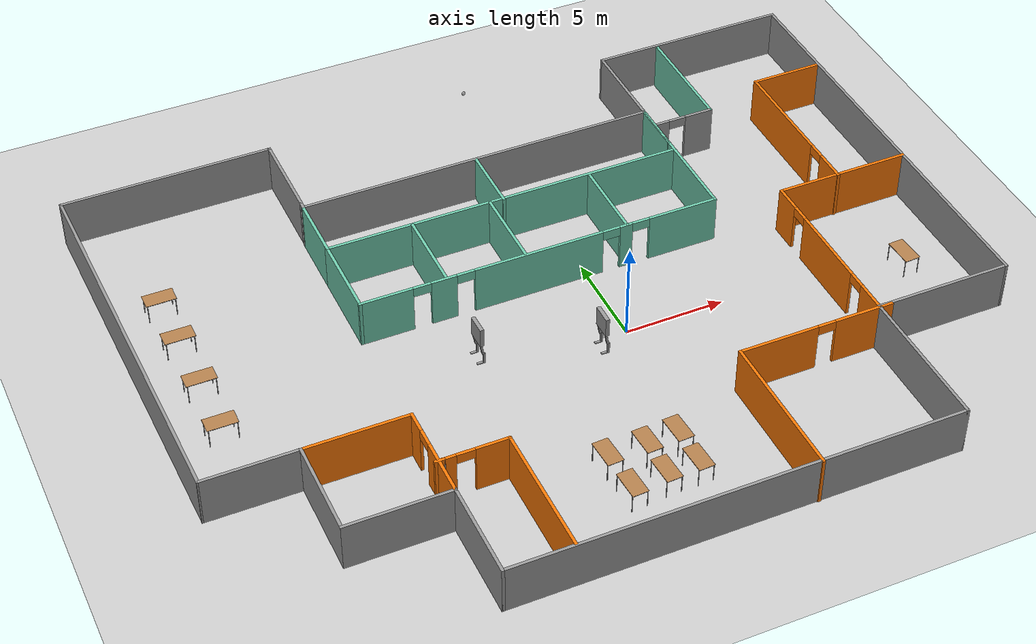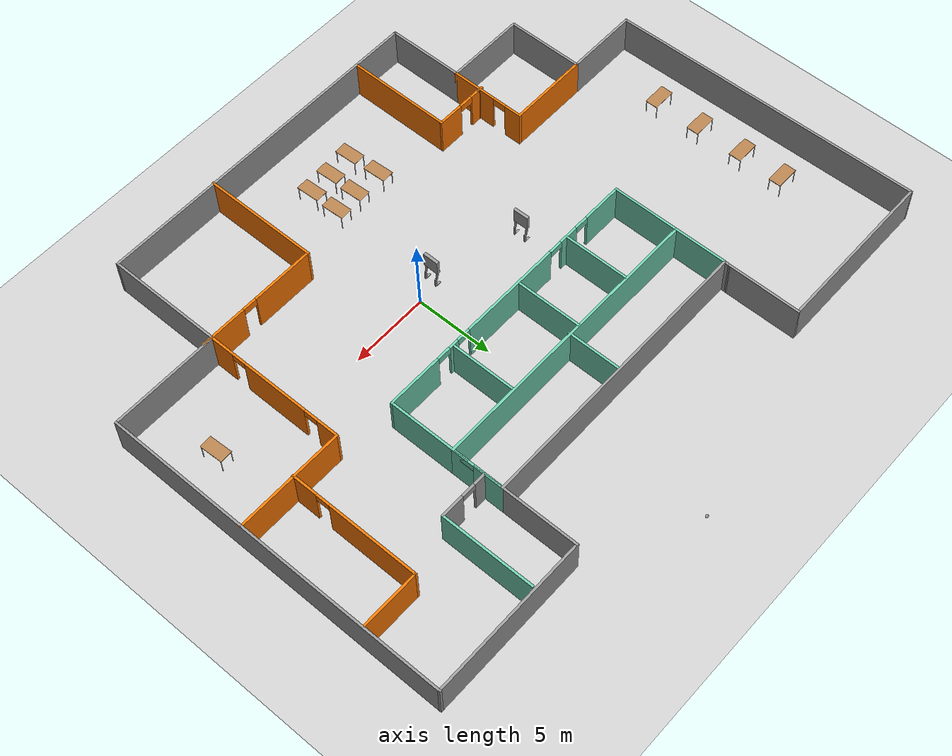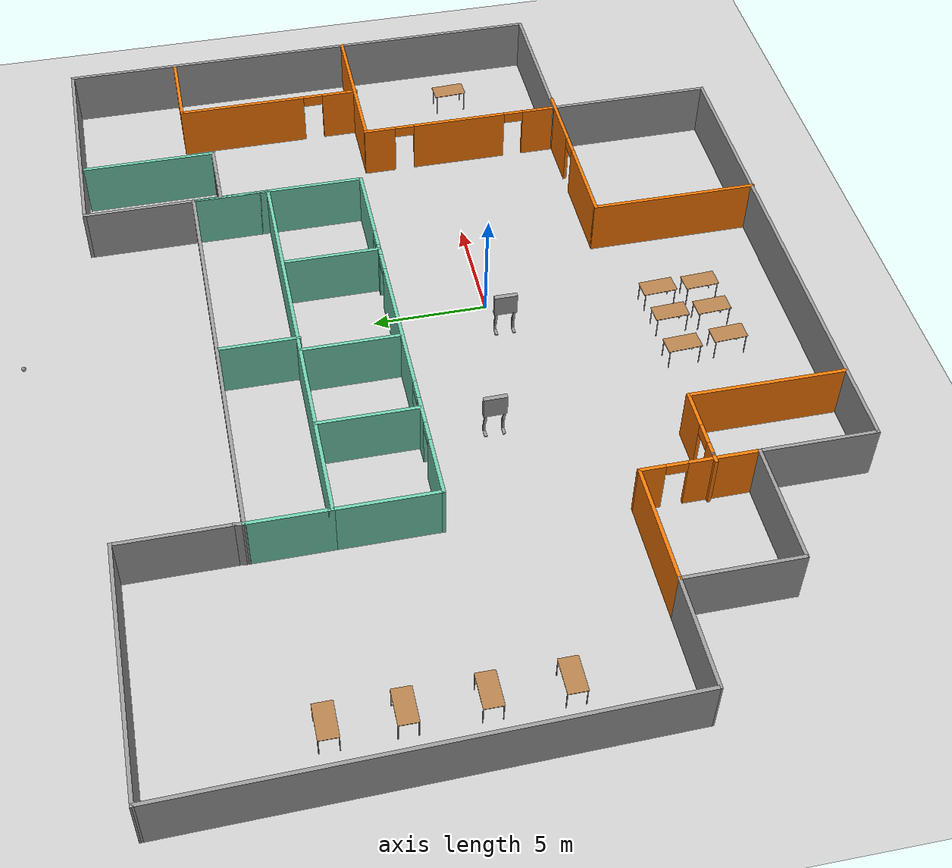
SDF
<sdf version="1.7">
 <world name="default">
  <plugin name="hello" filename="libhello.so"/>
  <model name="building_">
   <pose>-2.6285 1.9601 0 0 -0 0</pose>
   <link name="Wall_13">
    <collision name="Wall_13_Collision">
     <geometry><box><size>20.2535 0.15 2.5</size></box></geometry>
     <pose>0 0 1.25 0 -0 0</pose>
    </collision>
    <visual name="Wall_13_Visual">
     <pose>0 0 1.25 0 -0 0</pose>
     <geometry><box><size>20.2535 0.15 2.5</size></box></geometry>
     <material>
      <script><uri>file://media/materials/scripts/gazebo.material</uri><name>Gazebo/Grey</name></script>
      <ambient>1 1 1 1</ambient>
     </material>
     <meta><layer>0</layer></meta>
    </visual>
    <pose>-19.3243 4.87461 0 0 0 -1.55218</pose>
   </link>
   <link name="Wall_14">
    <collision name="Wall_14_Collision">
     <geometry><box><size>4.75 0.15 2.5</size></box></geometry>
     <pose>0 0 1.25 0 -0 0</pose>
    </collision>
    <visual name="Wall_14_Visual">
     <pose>0 0 1.25 0 -0 0</pose>
     <geometry><box><size>4.75 0.15 2.5</size></box></geometry>
     <material>
      <script><uri>file://media/materials/scripts/gazebo.material</uri><name>Gazebo/Grey</name></script>
      <ambient>1 1 1 1</ambient>
     </material>
     <meta><layer>0</layer></meta>
    </visual>
    <pose>-16.8372 -5.17539 0 0 -0 0</pose>
   </link>
   <link name="Wall_15">
    <collision name="Wall_15_Collision">
     <geometry><box><size>5 0.15 2.5</size></box></geometry>
     <pose>0 0 1.25 0 -0 0</pose>
    </collision>
    <visual name="Wall_15_Visual">
     <pose>0 0 1.25 0 -0 0</pose>
     <geometry><box><size>5 0.15 2.5</size></box></geometry>
     <material>
      <script><uri>file://media/materials/scripts/gazebo.material</uri><name>Gazebo/Grey</name></script>
      <ambient>1 1 1 1</ambient>
     </material>
     <meta><layer>0</layer></meta>
    </visual>
    <pose>-14.5372 -7.60039 0 0 0 -1.5708</pose>
   </link>
   <link name="Wall_16">
    <collision name="Wall_16_Collision">
     <geometry><box><size>5.25 0.15 2.5</size></box></geometry>
     <pose>0 0 1.25 0 -0 0</pose>
    </collision>
    <visual name="Wall_16_Visual">
     <pose>0 0 1.25 0 -0 0</pose>
     <geometry><box><size>5.25 0.15 2.5</size></box></geometry>
     <material>
      <script><uri>file://media/materials/scripts/gazebo.material</uri><name>Gazebo/Grey</name></script>
      <ambient>1 1 1 1</ambient>
     </material>
     <meta><layer>0</layer></meta>
    </visual>
    <pose>-11.9872 -10.0254 0 0 -0 0</pose>
   </link>
   <link name="Wall_17">
    <collision name="Wall_17_Collision">
     <geometry><box><size>5 0.15 2.5</size></box></geometry>
     <pose>0 0 1.25 0 -0 0</pose>
    </collision>
    <visual name="Wall_17_Visual">
     <pose>0 0 1.25 0 -0 0</pose>
     <geometry><box><size>5 0.15 2.5</size></box></geometry>
     <material>
      <script><uri>file://media/materials/scripts/gazebo.material</uri><name>Gazebo/Grey</name></script>
      <ambient>1 1 1 1</ambient>
     </material>
     <meta><layer>0</layer></meta>
    </visual>
    <pose>-9.43716 -12.4504 0 0 0 -1.5708</pose>
   </link>
   <link name="Wall_18">
    <collision name="Wall_18_Collision">
     <geometry><box><size>22.25 0.15 2.5</size></box></geometry>
     <pose>0 0 1.25 0 -0 0</pose>
    </collision>
    <visual name="Wall_18_Visual">
     <pose>0 0 1.25 0 -0 0</pose>
     <geometry><box><size>22.25 0.15 2.5</size></box></geometry>
     <material>
      <script><uri>file://media/materials/scripts/gazebo.material</uri><name>Gazebo/Grey</name></script>
      <ambient>1 1 1 1</ambient>
     </material>
     <meta><layer>0</layer></meta>
    </visual>
    <pose>1.61284 -14.8754 0 0 -0 0</pose>
   </link>
   <link name="Wall_19">
    <collision name="Wall_19_Collision">
     <geometry><box><size>7.5 0.15 2.5</size></box></geometry>
     <pose>0 0 1.25 0 -0 0</pose>
    </collision>
    <visual name="Wall_19_Visual">
     <pose>0 0 1.25 0 -0 0</pose>
     <geometry><box><size>7.5 0.15 2.5</size></box></geometry>
     <material>
      <script><uri>file://media/materials/scripts/gazebo.material</uri><name>Gazebo/Grey</name></script>
      <ambient>1 1 1 1</ambient>
     </material>
     <meta><layer>0</layer></meta>
    </visual>
    <pose>12.6628 -11.2004 0 0 -0 1.5708</pose>
   </link>
   <link name="Wall_20">
    <collision name="Wall_20_Collision">
     <geometry><box><size>7 0.15 2.5</size></box></geometry>
     <pose>0 0 1.25 0 -0 0</pose>
    </collision>
    <visual name="Wall_20_Visual">
     <pose>0 0 1.25 0 -0 0</pose>
     <geometry><box><size>7 0.15 2.5</size></box></geometry>
     <material>
      <script><uri>file://media/materials/scripts/gazebo.material</uri><name>Gazebo/Grey</name></script>
      <ambient>1 1 1 1</ambient>
     </material>
     <meta><layer>0</layer></meta>
    </visual>
    <pose>16.0878 -7.52539 0 0 -0 0</pose>
   </link>
   <link name="Wall_21">
    <collision name="Wall_21_Collision">
     <geometry><box><size>22.5 0.15 2.5</size></box></geometry>
     <pose>0 0 1.25 0 -0 0</pose>
    </collision>
    <visual name="Wall_21_Visual">
     <pose>0 0 1.25 0 -0 0</pose>
     <geometry><box><size>22.5 0.15 2.5</size></box></geometry>
     <material>
      <script><uri>file://media/materials/scripts/gazebo.material</uri><name>Gazebo/Grey</name></script>
      <ambient>1 1 1 1</ambient>
     </material>
     <meta><layer>0</layer></meta>
    </visual>
    <pose>19.5128 3.64961 0 0 -0 1.5708</pose>
   </link>
   <link name="Wall_22">
    <collision name="Wall_22_Collision">
     <geometry><box><size>10.25 0.15 2.5</size></box></geometry>
     <pose>0 0 1.25 0 -0 0</pose>
    </collision>
    <visual name="Wall_22_Visual">
     <pose>0 0 1.25 0 -0 0</pose>
     <geometry><box><size>10.25 0.15 2.5</size></box></geometry>
     <material>
      <script><uri>file://media/materials/scripts/gazebo.material</uri><name>Gazebo/Grey</name></script>
      <ambient>1 1 1 1</ambient>
     </material>
     <meta><layer>0</layer></meta>
    </visual>
    <pose>14.4628 14.8246 0 0 -0 3.14159</pose>
   </link>
   <link name="Wall_23">
    <collision name="Wall_23_Collision">
     <geometry><box><size>5 0.15 2.5</size></box></geometry>
     <pose>0 0 1.25 0 -0 0</pose>
    </collision>
    <visual name="Wall_23_Visual">
     <pose>0 0 1.25 0 -0 0</pose>
     <geometry><box><size>5 0.15 2.5</size></box></geometry>
     <material>
      <script><uri>file://media/materials/scripts/gazebo.material</uri><name>Gazebo/Grey</name></script>
      <ambient>1 1 1 1</ambient>
     </material>
     <meta><layer>0</layer></meta>
    </visual>
    <pose>9.41284 12.3996 0 0 0 -1.5708</pose>
   </link>
   <link name="Wall_24">
    <collision name="Wall_24_Collision">
     <geometry><box><size>18.5 0.15 2.5</size></box></geometry>
     <pose>0 0 1.25 0 -0 0</pose>
    </collision>
    <visual name="Wall_24_Visual">
     <pose>0 0 1.25 0 -0 0</pose>
     <geometry><box><size>18.5 0.15 2.5</size></box></geometry>
     <material>
      <script><uri>file://media/materials/scripts/gazebo.material</uri><name>Gazebo/Grey</name></script>
      <ambient>1 1 1 1</ambient>
     </material>
     <meta><layer>0</layer></meta>
    </visual>
    <pose>0.237843 9.97461 0 0 -0 3.14159</pose>
   </link>
   <link name="Wall_29">
    <collision name="Wall_29_Collision">
     <geometry><box><size>10.75 0.15 2.5</size></box></geometry>
     <pose>0 0 1.25 0 -0 0</pose>
    </collision>
    <visual name="Wall_29_Visual">
     <pose>0 0 1.25 0 -0 0</pose>
     <geometry><box><size>10.75 0.15 2.5</size></box></geometry>
     <material>
      <script><uri>file://media/materials/scripts/gazebo.material</uri><name>Gazebo/Grey</name></script>
      <ambient>1 1 1 1</ambient>
     </material>
     <meta><layer>0</layer></meta>
    </visual>
    <pose>-14.2115 14.9246 0 0 -0 0</pose>
   </link>
   <link name="Wall_30">
    <collision name="Wall_30_Collision">
     <geometry><box><size>4.75 0.15 2.5</size></box></geometry>
     <pose>0 0 1.25 0 -0 0</pose>
    </collision>
    <visual name="Wall_30_Visual">
     <pose>0 0 1.25 0 -0 0</pose>
     <geometry><box><size>4.75 0.15 2.5</size></box></geometry>
     <material>
      <script><uri>file://media/materials/scripts/gazebo.material</uri><name>Gazebo/Grey</name></script>
      <ambient>1 1 1 1</ambient>
     </material>
     <meta><layer>0</layer></meta>
    </visual>
    <pose>-8.91146 12.6246 0 0 0 -1.5708</pose>
   </link>
   <link name="Wall_31">
    <collision name="Wall_31_Collision">
     <geometry><box><size>0.5 0.15 2.5</size></box></geometry>
     <pose>0 0 1.25 0 -0 0</pose>
    </collision>
    <visual name="Wall_31_Visual">
     <pose>0 0 1.25 0 -0 0</pose>
     <geometry><box><size>0.5 0.15 2.5</size></box></geometry>
     <material>
      <script><uri>file://media/materials/scripts/gazebo.material</uri><name>Gazebo/Grey</name></script>
      <ambient>1 1 1 1</ambient>
     </material>
     <meta><layer>0</layer></meta>
    </visual>
    <pose>-8.92431 10.1496 0 0 0 -1.64408</pose>
   </link>
   <link name="Wall_33">
    <collision name="Wall_33_Collision">
     <geometry><box><size>3.5 0.15 2.5</size></box></geometry>
     <pose>0 0 1.25 0 -0 0</pose>
    </collision>
    <visual name="Wall_33_Visual">
     <pose>0 0 1.25 0 -0 0</pose>
     <geometry><box><size>3.5 0.15 2.5</size></box></geometry>
     <material>
      <script><uri>file://media/materials/scripts/gazebo.material</uri><name>Gazebo/Grey</name></script>
      <ambient>0.435294 0.796078 0.67451 1</ambient>
     </material>
     <meta><layer>0</layer></meta>
    </visual>
    <pose>-8.93716 8.29961 0 0 0 -1.5708</pose>
   </link>
   <link name="Wall_34">
    <collision name="Wall_34_Collision">
     <geometry><box><size>18.5 0.15 2.5</size></box></geometry>
     <pose>0 0 1.25 0 -0 0</pose>
    </collision>
    <visual name="Wall_34_Visual">
     <pose>0 0 1.25 0 -0 0</pose>
     <geometry><box><size>18.5 0.15 2.5</size></box></geometry>
     <material>
      <script><uri>file://media/materials/scripts/gazebo.material</uri><name>Gazebo/Grey</name></script>
      <ambient>0.435294 0.796078 0.67451 1</ambient>
     </material>
     <meta><layer>0</layer></meta>
    </visual>
    <pose>0.237843 6.62461 0 0 -0 0</pose>
   </link>
   <link name="Wall_35">
    <collision name="Wall_35_Collision">
     <geometry><box><size>3.5 0.15 2.5</size></box></geometry>
     <pose>0 0 1.25 0 -0 0</pose>
    </collision>
    <visual name="Wall_35_Visual">
     <pose>0 0 1.25 0 -0 0</pose>
     <geometry><box><size>3.5 0.15 2.5</size></box></geometry>
     <material>
      <script><uri>file://media/materials/scripts/gazebo.material</uri><name>Gazebo/Grey</name></script>
      <ambient>0.435294 0.796078 0.67451 1</ambient>
     </material>
     <meta><layer>0</layer></meta>
    </visual>
    <pose>9.41284 8.29961 0 0 -0 1.5708</pose>
   </link>
   <link name="Wall_36">
    <pose>9.41284 6.17461 0 0 0 -1.5708</pose>
    <visual name="Wall_36_Visual_0">
     <pose>-2.87314 0 1.25 0 -0 0</pose>
     <geometry><box><size>2.00371 0.15 2.5</size></box></geometry>
     <material>
      <script><uri>file://media/materials/scripts/gazebo.material</uri><name>Gazebo/Grey</name></script>
      <ambient>0.435294 0.796078 0.67451 1</ambient>
     </material>
     <meta><layer>0</layer></meta>
    </visual>
    <collision name="Wall_36_Collision_0">
     <geometry><box><size>2.00371 0.15 2.5</size></box></geometry>
     <pose>-2.87314 0 1.25 0 -0 0</pose>
    </collision>
    <visual name="Wall_36_Visual_1">
     <pose>1.45186 0 1.25 0 -0 0</pose>
     <geometry><box><size>4.84629 0.15 2.5</size></box></geometry>
     <material>
      <script><uri>file://media/materials/scripts/gazebo.material</uri><name>Gazebo/Grey</name></script>
      <ambient>0.435294 0.796078 0.67451 1</ambient>
     </material>
     <meta><layer>0</layer></meta>
    </visual>
    <collision name="Wall_36_Collision_1">
     <geometry><box><size>4.84629 0.15 2.5</size></box></geometry>
     <pose>1.45186 0 1.25 0 -0 0</pose>
    </collision>
    <visual name="Wall_36_Visual_2">
     <pose>-1.42129 0 2.25 0 -0 0</pose>
     <geometry><box><size>0.9 0.15 0.5</size></box></geometry>
     <material>
      <script><uri>file://media/materials/scripts/gazebo.material</uri><name>Gazebo/Grey</name></script>
      <ambient>0.435294 0.796078 0.67451 1</ambient>
     </material>
     <meta><layer>0</layer></meta>
    </visual>
    <collision name="Wall_36_Collision_2">
     <geometry><box><size>0.9 0.15 0.5</size></box></geometry>
     <pose>-1.42129 0 2.25 0 -0 0</pose>
    </collision>
   </link>
   <link name="Wall_37">
    <pose>0.237843 2.37461 0 0 -0 3.14159</pose>
    <visual name="Wall_37_Visual_0">
     <pose>-7.43929 0 1.25 0 -0 0</pose>
     <geometry><box><size>3.62143 0.15 2.5</size></box></geometry>
     <material>
      <script><uri>file://media/materials/scripts/gazebo.material</uri><name>Gazebo/Grey</name></script>
      <ambient>0.435294 0.796078 0.67451 1</ambient>
     </material>
     <meta><layer>0</layer></meta>
    </visual>
    <collision name="Wall_37_Collision_0">
     <geometry><box><size>3.62143 0.15 2.5</size></box></geometry>
     <pose>-7.43929 0 1.25 0 -0 0</pose>
    </collision>
    <visual name="Wall_37_Visual_1">
     <pose>-4.40279 0 1.25 0 -0 0</pose>
     <geometry><box><size>0.651573 0.15 2.5</size></box></geometry>
     <material>
      <script><uri>file://media/materials/scripts/gazebo.material</uri><name>Gazebo/Grey</name></script>
      <ambient>0.435294 0.796078 0.67451 1</ambient>
     </material>
     <meta><layer>0</layer></meta>
    </visual>
    <collision name="Wall_37_Collision_1">
     <geometry><box><size>0.651573 0.15 2.5</size></box></geometry>
     <pose>-4.40279 0 1.25 0 -0 0</pose>
    </collision>
    <visual name="Wall_37_Visual_2">
     <pose>0.144925 0 1.25 0 -0 0</pose>
     <geometry><box><size>6.64385 0.15 2.5</size></box></geometry>
     <material>
      <script><uri>file://media/materials/scripts/gazebo.material</uri><name>Gazebo/Grey</name></script>
      <ambient>0.435294 0.796078 0.67451 1</ambient>
     </material>
     <meta><layer>0</layer></meta>
    </visual>
    <collision name="Wall_37_Collision_2">
     <geometry><box><size>6.64385 0.15 2.5</size></box></geometry>
     <pose>0.144925 0 1.25 0 -0 0</pose>
    </collision>
    <visual name="Wall_37_Visual_3">
     <pose>5.01365 0 1.25 0 -0 0</pose>
     <geometry><box><size>1.2936 0.15 2.5</size></box></geometry>
     <material>
      <script><uri>file://media/materials/scripts/gazebo.material</uri><name>Gazebo/Grey</name></script>
      <ambient>0.435294 0.796078 0.67451 1</ambient>
     </material>
     <meta><layer>0</layer></meta>
    </visual>
    <collision name="Wall_37_Collision_3">
     <geometry><box><size>1.2936 0.15 2.5</size></box></geometry>
     <pose>5.01365 0 1.25 0 -0 0</pose>
    </collision>
    <visual name="Wall_37_Visual_4">
     <pose>7.90523 0 1.25 0 -0 0</pose>
     <geometry><box><size>2.68955 0.15 2.5</size></box></geometry>
     <material>
      <script><uri>file://media/materials/scripts/gazebo.material</uri><name>Gazebo/Grey</name></script>
      <ambient>0.435294 0.796078 0.67451 1</ambient>
     </material>
     <meta><layer>0</layer></meta>
    </visual>
    <collision name="Wall_37_Collision_4">
     <geometry><box><size>2.68955 0.15 2.5</size></box></geometry>
     <pose>7.90523 0 1.25 0 -0 0</pose>
    </collision>
    <visual name="Wall_37_Visual_5">
     <pose>-5.17857 0 2.25 0 -0 0</pose>
     <geometry><box><size>0.9 0.15 0.5</size></box></geometry>
     <material>
      <script><uri>file://media/materials/scripts/gazebo.material</uri><name>Gazebo/Grey</name></script>
      <ambient>0.435294 0.796078 0.67451 1</ambient>
     </material>
     <meta><layer>0</layer></meta>
    </visual>
    <collision name="Wall_37_Collision_5">
     <geometry><box><size>0.9 0.15 0.5</size></box></geometry>
     <pose>-5.17857 0 2.25 0 -0 0</pose>
    </collision>
    <visual name="Wall_37_Visual_6">
     <pose>-3.627 0 2.25 0 -0 0</pose>
     <geometry><box><size>0.9 0.15 0.5</size></box></geometry>
     <material>
      <script><uri>file://media/materials/scripts/gazebo.material</uri><name>Gazebo/Grey</name></script>
      <ambient>0.435294 0.796078 0.67451 1</ambient>
     </material>
     <meta><layer>0</layer></meta>
    </visual>
    <collision name="Wall_37_Collision_6">
     <geometry><box><size>0.9 0.15 0.5</size></box></geometry>
     <pose>-3.627 0 2.25 0 -0 0</pose>
    </collision>
    <visual name="Wall_37_Visual_7">
     <pose>3.91685 0 2.25 0 -0 0</pose>
     <geometry><box><size>0.9 0.15 0.5</size></box></geometry>
     <material>
      <script><uri>file://media/materials/scripts/gazebo.material</uri><name>Gazebo/Grey</name></script>
      <ambient>0.435294 0.796078 0.67451 1</ambient>
     </material>
     <meta><layer>0</layer></meta>
    </visual>
    <collision name="Wall_37_Collision_7">
     <geometry><box><size>0.9 0.15 0.5</size></box></geometry>
     <pose>3.91685 0 2.25 0 -0 0</pose>
    </collision>
    <visual name="Wall_37_Visual_8">
     <pose>6.11045 0 2.25 0 -0 0</pose>
     <geometry><box><size>0.9 0.15 0.5</size></box></geometry>
     <material>
      <script><uri>file://media/materials/scripts/gazebo.material</uri><name>Gazebo/Grey</name></script>
      <ambient>0.435294 0.796078 0.67451 1</ambient>
     </material>
     <meta><layer>0</layer></meta>
    </visual>
    <collision name="Wall_37_Collision_8">
     <geometry><box><size>0.9 0.15 0.5</size></box></geometry>
     <pose>6.11045 0 2.25 0 -0 0</pose>
    </collision>
   </link>
   <link name="Wall_38">
    <collision name="Wall_38_Collision">
     <geometry><box><size>4.5 0.15 2.5</size></box></geometry>
     <pose>0 0 1.25 0 -0 0</pose>
    </collision>
    <visual name="Wall_38_Visual">
     <pose>0 0 1.25 0 -0 0</pose>
     <geometry><box><size>4.5 0.15 2.5</size></box></geometry>
     <material>
      <script><uri>file://media/materials/scripts/gazebo.material</uri><name>Gazebo/Grey</name></script>
      <ambient>0.435294 0.796078 0.67451 1</ambient>
     </material>
     <meta><layer>0</layer></meta>
    </visual>
    <pose>-8.93716 4.54961 0 0 -0 1.5708</pose>
   </link>
   <link name="Wall_40">
    <collision name="Wall_40_Collision">
     <geometry><box><size>3.5 0.15 2.5</size></box></geometry>
     <pose>0 0 1.25 0 -0 0</pose>
    </collision>
    <visual name="Wall_40_Visual">
     <pose>0 0 1.25 0 -0 0</pose>
     <geometry><box><size>3.5 0.15 2.5</size></box></geometry>
     <material>
      <script><uri>file://media/materials/scripts/gazebo.material</uri><name>Gazebo/Grey</name></script>
      <ambient>0.435294 0.796078 0.67451 1</ambient>
     </material>
     <meta><layer>0</layer></meta>
    </visual>
    <pose>0.11744 8.24588 0 0 -0 1.5708</pose>
   </link>
   <link name="Wall_43">
    <collision name="Wall_43_Collision">
     <geometry><box><size>4.25 0.15 2.5</size></box></geometry>
     <pose>0 0 1.25 0 -0 0</pose>
    </collision>
    <visual name="Wall_43_Visual">
     <pose>0 0 1.25 0 -0 0</pose>
     <geometry><box><size>4.25 0.15 2.5</size></box></geometry>
     <material>
      <script><uri>file://media/materials/scripts/gazebo.material</uri><name>Gazebo/Grey</name></script>
      <ambient>0.435294 0.796078 0.67451 1</ambient>
     </material>
     <meta><layer>0</layer></meta>
    </visual>
    <pose>-0.590131 4.52088 0 0 0 -1.5708</pose>
   </link>
   <link name="Wall_45">
    <collision name="Wall_45_Collision">
     <geometry><box><size>4.25 0.15 2.5</size></box></geometry>
     <pose>0 0 1.25 0 -0 0</pose>
    </collision>
    <visual name="Wall_45_Visual">
     <pose>0 0 1.25 0 -0 0</pose>
     <geometry><box><size>4.25 0.15 2.5</size></box></geometry>
     <material>
      <script><uri>file://media/materials/scripts/gazebo.material</uri><name>Gazebo/Grey</name></script>
      <ambient>0.435294 0.796078 0.67451 1</ambient>
     </material>
     <meta><layer>0</layer></meta>
    </visual>
    <pose>-4.62328 4.52088 0 0 0 -1.5708</pose>
   </link>
   <link name="Wall_49">
    <pose>11.0074 8.76435 0 0 -0 0</pose>
    <visual name="Wall_49_Visual_0">
     <pose>-1.21135 0 1.25 0 -0 0</pose>
     <geometry><box><size>0.827291 0.15 2.5</size></box></geometry>
     <material>
      <script><uri>file://media/materials/scripts/gazebo.material</uri><name>Gazebo/Grey</name></script>
      <ambient>1 1 1 1</ambient>
     </material>
     <meta><layer>0</layer></meta>
    </visual>
    <collision name="Wall_49_Collision_0">
     <geometry><box><size>0.827291 0.15 2.5</size></box></geometry>
     <pose>-1.21135 0 1.25 0 -0 0</pose>
    </collision>
    <visual name="Wall_49_Visual_1">
     <pose>0.863645 0 1.25 0 -0 0</pose>
     <geometry><box><size>1.52271 0.15 2.5</size></box></geometry>
     <material>
      <script><uri>file://media/materials/scripts/gazebo.material</uri><name>Gazebo/Grey</name></script>
      <ambient>1 1 1 1</ambient>
     </material>
     <meta><layer>0</layer></meta>
    </visual>
    <collision name="Wall_49_Collision_1">
     <geometry><box><size>1.52271 0.15 2.5</size></box></geometry>
     <pose>0.863645 0 1.25 0 -0 0</pose>
    </collision>
    <visual name="Wall_49_Visual_2">
     <pose>-0.347709 0 2.25 0 -0 0</pose>
     <geometry><box><size>0.9 0.15 0.5</size></box></geometry>
     <material>
      <script><uri>file://media/materials/scripts/gazebo.material</uri><name>Gazebo/Grey</name></script>
      <ambient>1 1 1 1</ambient>
     </material>
     <meta><layer>0</layer></meta>
    </visual>
    <collision name="Wall_49_Collision_2">
     <geometry><box><size>0.9 0.15 0.5</size></box></geometry>
     <pose>-0.347709 0 2.25 0 -0 0</pose>
    </collision>
   </link>
   <link name="Wall_50">
    <collision name="Wall_50_Collision">
     <geometry><box><size>6 0.15 2.5</size></box></geometry>
     <pose>0 0 1.25 0 -0 0</pose>
    </collision>
    <visual name="Wall_50_Visual">
     <pose>0 0 1.25 0 -0 0</pose>
     <geometry><box><size>6 0.15 2.5</size></box></geometry>
     <material>
      <script><uri>file://media/materials/scripts/gazebo.material</uri><name>Gazebo/Grey</name></script>
      <ambient>0.435294 0.796078 0.67451 1</ambient>
     </material>
     <meta><layer>0</layer></meta>
    </visual>
    <pose>12.5574 11.6894 0 0 -0 1.5708</pose>
   </link>
   <link name="Wall_52">
    <collision name="Wall_52_Collision">
     <geometry><box><size>4.25 0.15 2.5</size></box></geometry>
     <pose>0 0 1.25 0 -0 0</pose>
    </collision>
    <visual name="Wall_52_Visual">
     <pose>0 0 1.25 0 -0 0</pose>
     <geometry><box><size>4.25 0.15 2.5</size></box></geometry>
     <material>
      <script><uri>file://media/materials/scripts/gazebo.material</uri><name>Gazebo/Grey</name></script>
      <ambient>0.435294 0.796078 0.67451 1</ambient>
     </material>
     <meta><layer>0</layer></meta>
    </visual>
    <pose>4.69144 4.42852 0 0 -0 1.5708</pose>
   </link>
   <link name="Wall_54">
    <collision name="Wall_54_Collision">
     <geometry><box><size>7.5 0.15 2.5</size></box></geometry>
     <pose>0 0 1.25 0 -0 0</pose>
    </collision>
    <visual name="Wall_54_Visual">
     <pose>0 0 1.25 0 -0 0</pose>
     <geometry><box><size>7.5 0.15 2.5</size></box></geometry>
     <material>
      <script><uri>file://media/materials/scripts/gazebo.material</uri><name>Gazebo/Grey</name></script>
      <ambient>0.996078 0.47451 0.0196078 1</ambient>
     </material>
     <meta><layer>0</layer></meta>
    </visual>
    <pose>5.42366 -11.251 0 0 -0 1.5708</pose>
   </link>
   <link name="Wall_55">
    <pose>9.34866 -7.576 0 0 -0 0</pose>
    <visual name="Wall_55_Visual_0">
     <pose>-1.96254 0 1.25 0 -0 0</pose>
     <geometry><box><size>4.07492 0.15 2.5</size></box></geometry>
     <material>
      <script><uri>file://media/materials/scripts/gazebo.material</uri><name>Gazebo/Grey</name></script>
      <ambient>0.996078 0.47451 0.0196078 1</ambient>
     </material>
     <meta><layer>0</layer></meta>
    </visual>
    <collision name="Wall_55_Collision_0">
     <geometry><box><size>4.07492 0.15 2.5</size></box></geometry>
     <pose>-1.96254 0 1.25 0 -0 0</pose>
    </collision>
    <visual name="Wall_55_Visual_1">
     <pose>2.48746 0 1.25 0 -0 0</pose>
     <geometry><box><size>3.02508 0.15 2.5</size></box></geometry>
     <material>
      <script><uri>file://media/materials/scripts/gazebo.material</uri><name>Gazebo/Grey</name></script>
      <ambient>0.996078 0.47451 0.0196078 1</ambient>
     </material>
     <meta><layer>0</layer></meta>
    </visual>
    <collision name="Wall_55_Collision_1">
     <geometry><box><size>3.02508 0.15 2.5</size></box></geometry>
     <pose>2.48746 0 1.25 0 -0 0</pose>
    </collision>
    <visual name="Wall_55_Visual_2">
     <pose>0.52492 0 2.25 0 -0 0</pose>
     <geometry><box><size>0.9 0.15 0.5</size></box></geometry>
     <material>
      <script><uri>file://media/materials/scripts/gazebo.material</uri><name>Gazebo/Grey</name></script>
      <ambient>0.996078 0.47451 0.0196078 1</ambient>
     </material>
     <meta><layer>0</layer></meta>
    </visual>
    <collision name="Wall_55_Collision_2">
     <geometry><box><size>0.9 0.15 0.5</size></box></geometry>
     <pose>0.52492 0 2.25 0 -0 0</pose>
    </collision>
   </link>
   <link name="Wall_59">
    <pose>12.6628 -2.97539 0 0 -0 1.5708</pose>
    <visual name="Wall_59_Visual_0">
     <pose>-3.81206 0 1.25 0 -0 0</pose>
     <geometry><box><size>1.62589 0.15 2.5</size></box></geometry>
     <material>
      <script><uri>file://media/materials/scripts/gazebo.material</uri><name>Gazebo/Grey</name></script>
      <ambient>0.996078 0.47451 0.0196078 1</ambient>
     </material>
     <meta><layer>0</layer></meta>
    </visual>
    <collision name="Wall_59_Collision_0">
     <geometry><box><size>1.62589 0.15 2.5</size></box></geometry>
     <pose>-3.81206 0 1.25 0 -0 0</pose>
    </collision>
    <visual name="Wall_59_Visual_1">
     <pose>0.080501 0 1.25 0 -0 0</pose>
     <geometry><box><size>4.35923 0.15 2.5</size></box></geometry>
     <material>
      <script><uri>file://media/materials/scripts/gazebo.material</uri><name>Gazebo/Grey</name></script>
      <ambient>0.996078 0.47451 0.0196078 1</ambient>
     </material>
     <meta><layer>0</layer></meta>
    </visual>
    <collision name="Wall_59_Collision_1">
     <geometry><box><size>4.35923 0.15 2.5</size></box></geometry>
     <pose>0.080501 0 1.25 0 -0 0</pose>
    </collision>
    <visual name="Wall_59_Visual_2">
     <pose>3.89256 0 1.25 0 -0 0</pose>
     <geometry><box><size>1.46489 0.15 2.5</size></box></geometry>
     <material>
      <script><uri>file://media/materials/scripts/gazebo.material</uri><name>Gazebo/Grey</name></script>
      <ambient>0.996078 0.47451 0.0196078 1</ambient>
     </material>
     <meta><layer>0</layer></meta>
    </visual>
    <collision name="Wall_59_Collision_2">
     <geometry><box><size>1.46489 0.15 2.5</size></box></geometry>
     <pose>3.89256 0 1.25 0 -0 0</pose>
    </collision>
    <visual name="Wall_59_Visual_3">
     <pose>-2.54911 0 2.25 0 -0 0</pose>
     <geometry><box><size>0.9 0.15 0.5</size></box></geometry>
     <material>
      <script><uri>file://media/materials/scripts/gazebo.material</uri><name>Gazebo/Grey</name></script>
      <ambient>0.996078 0.47451 0.0196078 1</ambient>
     </material>
     <meta><layer>0</layer></meta>
    </visual>
    <collision name="Wall_59_Collision_3">
     <geometry><box><size>0.9 0.15 0.5</size></box></geometry>
     <pose>-2.54911 0 2.25 0 -0 0</pose>
    </collision>
    <visual name="Wall_59_Visual_4">
     <pose>2.71011 0 2.25 0 -0 0</pose>
     <geometry><box><size>0.9 0.15 0.5</size></box></geometry>
     <material>
      <script><uri>file://media/materials/scripts/gazebo.material</uri><name>Gazebo/Grey</name></script>
      <ambient>0.996078 0.47451 0.0196078 1</ambient>
     </material>
     <meta><layer>0</layer></meta>
    </visual>
    <collision name="Wall_59_Collision_4">
     <geometry><box><size>0.9 0.15 0.5</size></box></geometry>
     <pose>2.71011 0 2.25 0 -0 0</pose>
    </collision>
   </link>
   <link name="Wall_60">
    <collision name="Wall_60_Collision">
     <geometry><box><size>7 0.15 2.5</size></box></geometry>
     <pose>0 0 1.25 0 -0 0</pose>
    </collision>
    <visual name="Wall_60_Visual">
     <pose>0 0 1.25 0 -0 0</pose>
     <geometry><box><size>7 0.15 2.5</size></box></geometry>
     <material>
      <script><uri>file://media/materials/scripts/gazebo.material</uri><name>Gazebo/Grey</name></script>
      <ambient>0.996078 0.47451 0.0196078 1</ambient>
     </material>
     <meta><layer>0</layer></meta>
    </visual>
    <pose>16.0878 1.57461 0 0 -0 0</pose>
   </link>
   <link name="Wall_62">
    <pose>15.7952 5.70315 0 0 -0 1.5708</pose>
    <visual name="Wall_62_Visual_0">
     <pose>-3.39234 0 1.25 0 -0 0</pose>
     <geometry><box><size>1.71531 0.15 2.5</size></box></geometry>
     <material>
      <script><uri>file://media/materials/scripts/gazebo.material</uri><name>Gazebo/Grey</name></script>
      <ambient>0.996078 0.47451 0.0196078 1</ambient>
     </material>
     <meta><layer>0</layer></meta>
    </visual>
    <collision name="Wall_62_Collision_0">
     <geometry><box><size>1.71531 0.15 2.5</size></box></geometry>
     <pose>-3.39234 0 1.25 0 -0 0</pose>
    </collision>
    <visual name="Wall_62_Visual_1">
     <pose>1.30766 0 1.25 0 -0 0</pose>
     <geometry><box><size>5.88469 0.15 2.5</size></box></geometry>
     <material>
      <script><uri>file://media/materials/scripts/gazebo.material</uri><name>Gazebo/Grey</name></script>
      <ambient>0.996078 0.47451 0.0196078 1</ambient>
     </material>
     <meta><layer>0</layer></meta>
    </visual>
    <collision name="Wall_62_Collision_1">
     <geometry><box><size>5.88469 0.15 2.5</size></box></geometry>
     <pose>1.30766 0 1.25 0 -0 0</pose>
    </collision>
    <visual name="Wall_62_Visual_2">
     <pose>-2.08468 0 2.25 0 -0 0</pose>
     <geometry><box><size>0.9 0.15 0.5</size></box></geometry>
     <material>
      <script><uri>file://media/materials/scripts/gazebo.material</uri><name>Gazebo/Grey</name></script>
      <ambient>0.996078 0.47451 0.0196078 1</ambient>
     </material>
     <meta><layer>0</layer></meta>
    </visual>
    <collision name="Wall_62_Collision_2">
     <geometry><box><size>0.9 0.15 0.5</size></box></geometry>
     <pose>-2.08468 0 2.25 0 -0 0</pose>
    </collision>
   </link>
   <link name="Wall_63">
    <collision name="Wall_63_Collision">
     <geometry><box><size>3.75 0.15 2.5</size></box></geometry>
     <pose>0 0 1.25 0 -0 0</pose>
    </collision>
    <visual name="Wall_63_Visual">
     <pose>0 0 1.25 0 -0 0</pose>
     <geometry><box><size>3.75 0.15 2.5</size></box></geometry>
     <material>
      <script><uri>file://media/materials/scripts/gazebo.material</uri><name>Gazebo/Grey</name></script>
      <ambient>0.996078 0.47451 0.0196078 1</ambient>
     </material>
     <meta><layer>0</layer></meta>
    </visual>
    <pose>17.5952 9.87815 0 0 -0 0</pose>
   </link>
   <link name="Wall_65">
    <collision name="Wall_65_Collision">
     <geometry><box><size>6.75 0.15 2.5</size></box></geometry>
     <pose>0 0 1.25 0 -0 0</pose>
    </collision>
    <visual name="Wall_65_Visual">
     <pose>0 0 1.25 0 -0 0</pose>
     <geometry><box><size>6.75 0.15 2.5</size></box></geometry>
     <material>
      <script><uri>file://media/materials/scripts/gazebo.material</uri><name>Gazebo/Grey</name></script>
      <ambient>0.996078 0.47451 0.0196078 1</ambient>
     </material>
     <meta><layer>0</layer></meta>
    </visual>
    <pose>-6.1281 -11.5016 0 0 -0 1.5708</pose>
   </link>
   <link name="Wall_66">
    <pose>-7.6781 -8.20158 0 0 -0 3.14159</pose>
    <visual name="Wall_66_Visual_0">
     <pose>-0.778331 0 1.25 0 -0 0</pose>
     <geometry><box><size>1.69334 0.15 2.5</size></box></geometry>
     <material>
      <script><uri>file://media/materials/scripts/gazebo.material</uri><name>Gazebo/Grey</name></script>
      <ambient>0.996078 0.47451 0.0196078 1</ambient>
     </material>
     <meta><layer>0</layer></meta>
    </visual>
    <collision name="Wall_66_Collision_0">
     <geometry><box><size>1.69334 0.15 2.5</size></box></geometry>
     <pose>-0.778331 0 1.25 0 -0 0</pose>
    </collision>
    <visual name="Wall_66_Visual_1">
     <pose>1.29667 0 1.25 0 -0 0</pose>
     <geometry><box><size>0.656662 0.15 2.5</size></box></geometry>
     <material>
      <script><uri>file://media/materials/scripts/gazebo.material</uri><name>Gazebo/Grey</name></script>
      <ambient>0.996078 0.47451 0.0196078 1</ambient>
     </material>
     <meta><layer>0</layer></meta>
    </visual>
    <collision name="Wall_66_Collision_1">
     <geometry><box><size>0.656662 0.15 2.5</size></box></geometry>
     <pose>1.29667 0 1.25 0 -0 0</pose>
    </collision>
    <visual name="Wall_66_Visual_2">
     <pose>0.518338 0 2.25 0 -0 0</pose>
     <geometry><box><size>0.9 0.15 0.5</size></box></geometry>
     <material>
      <script><uri>file://media/materials/scripts/gazebo.material</uri><name>Gazebo/Grey</name></script>
      <ambient>0.996078 0.47451 0.0196078 1</ambient>
     </material>
     <meta><layer>0</layer></meta>
    </visual>
    <collision name="Wall_66_Collision_2">
     <geometry><box><size>0.9 0.15 0.5</size></box></geometry>
     <pose>0.518338 0 2.25 0 -0 0</pose>
    </collision>
   </link>
   <link name="Wall_67">
    <collision name="Wall_67_Collision">
     <geometry><box><size>0.15 0.15 2.5</size></box></geometry>
     <pose>0 0 1.25 0 -0 0</pose>
    </collision>
    <visual name="Wall_67_Visual">
     <pose>0 0 1.25 0 -0 0</pose>
     <geometry><box><size>0.15 0.15 2.5</size></box></geometry>
     <material>
      <script><uri>file://media/materials/scripts/gazebo.material</uri><name>Gazebo/Grey</name></script>
      <ambient>1 1 1 1</ambient>
     </material>
     <meta><layer>0</layer></meta>
    </visual>
    <pose>-9.2281 -8.20158 0 0 -0 0</pose>
   </link>
   <link name="Wall_68">
    <collision name="Wall_68_Collision">
     <geometry><box><size>0.5 0.15 2.5</size></box></geometry>
     <pose>0 0 1.25 0 -0 0</pose>
    </collision>
    <visual name="Wall_68_Visual">
     <pose>0 0 1.25 0 -0 0</pose>
     <geometry><box><size>0.5 0.15 2.5</size></box></geometry>
     <material>
      <script><uri>file://media/materials/scripts/gazebo.material</uri><name>Gazebo/Grey</name></script>
      <ambient>0.996078 0.47451 0.0196078 1</ambient>
     </material>
     <meta><layer>0</layer></meta>
    </visual>
    <pose>-9.4031 -8.20158 0 0 -0 3.14159</pose>
   </link>
   <link name="Wall_70">
    <collision name="Wall_70_Collision">
     <geometry><box><size>0.15 0.15 2.5</size></box></geometry>
     <pose>0 0 1.25 0 -0 0</pose>
    </collision>
    <visual name="Wall_70_Visual">
     <pose>0 0 1.25 0 -0 0</pose>
     <geometry><box><size>0.15 0.15 2.5</size></box></geometry>
     <material>
      <script><uri>file://media/materials/scripts/gazebo.material</uri><name>Gazebo/Grey</name></script>
      <ambient>1 1 1 1</ambient>
     </material>
     <meta><layer>0</layer></meta>
    </visual>
    <pose>-9.43716 -10.0254 0 0 -0 0</pose>
   </link>
   <link name="Wall_71">
    <pose>-9.43716 -7.60039 0 0 -0 1.5708</pose>
    <visual name="Wall_71_Visual_0">
     <pose>-1.02013 0 1.25 0 -0 0</pose>
     <geometry><box><size>2.95974 0.15 2.5</size></box></geometry>
     <material>
      <script><uri>file://media/materials/scripts/gazebo.material</uri><name>Gazebo/Grey</name></script>
      <ambient>0.996078 0.47451 0.0196078 1</ambient>
     </material>
     <meta><layer>0</layer></meta>
    </visual>
    <collision name="Wall_71_Collision_0">
     <geometry><box><size>2.95974 0.15 2.5</size></box></geometry>
     <pose>-1.02013 0 1.25 0 -0 0</pose>
    </collision>
    <visual name="Wall_71_Visual_1">
     <pose>1.92987 0 1.25 0 -0 0</pose>
     <geometry><box><size>1.14026 0.15 2.5</size></box></geometry>
     <material>
      <script><uri>file://media/materials/scripts/gazebo.material</uri><name>Gazebo/Grey</name></script>
      <ambient>0.996078 0.47451 0.0196078 1</ambient>
     </material>
     <meta><layer>0</layer></meta>
    </visual>
    <collision name="Wall_71_Collision_1">
     <geometry><box><size>1.14026 0.15 2.5</size></box></geometry>
     <pose>1.92987 0 1.25 0 -0 0</pose>
    </collision>
    <visual name="Wall_71_Visual_2">
     <pose>0.909739 0 2.25 0 -0 0</pose>
     <geometry><box><size>0.9 0.15 0.5</size></box></geometry>
     <material>
      <script><uri>file://media/materials/scripts/gazebo.material</uri><name>Gazebo/Grey</name></script>
      <ambient>0.996078 0.47451 0.0196078 1</ambient>
     </material>
     <meta><layer>0</layer></meta>
    </visual>
    <collision name="Wall_71_Collision_2">
     <geometry><box><size>0.9 0.15 0.5</size></box></geometry>
     <pose>0.909739 0 2.25 0 -0 0</pose>
    </collision>
   </link>
   <link name="Wall_72">
    <collision name="Wall_72_Collision">
     <geometry><box><size>5.25 0.15 2.5</size></box></geometry>
     <pose>0 0 1.25 0 -0 0</pose>
    </collision>
    <visual name="Wall_72_Visual">
     <pose>0 0 1.25 0 -0 0</pose>
     <geometry><box><size>5.25 0.15 2.5</size></box></geometry>
     <material>
      <script><uri>file://media/materials/scripts/gazebo.material</uri><name>Gazebo/Grey</name></script>
      <ambient>0.996078 0.47451 0.0196078 1</ambient>
     </material>
     <meta><layer>0</layer></meta>
    </visual>
    <pose>-11.9872 -5.17539 0 0 -0 3.14159</pose>
   </link>
   <static>1</static>
  </model>
  <light name="sun" type="directional">
   <pose>0 0 10 0 -0 0</pose>
   <diffuse>0.8 0.8 0.8 1</diffuse>
   <specular>0.2 0.2 0.2 1</specular>
   <attenuation>
    <range>1000</range>
    <constant>0.9</constant>
    <linear>0.01</linear>
    <quadratic>0.001</quadratic>
   </attenuation>
   <direction>-0.5 0.1 -0.9</direction>
   <spot><inner_angle>0</inner_angle><outer_angle>0</outer_angle><falloff>0</falloff></spot>
  </light>
  <model name="ground_plane">
   <static>1</static>
   <link name="link">
    <collision name="collision">
     <geometry><plane><normal>0 0 1</normal><size>100 100</size></plane></geometry>
     <surface>
      <contact><collide_bitmask>65535</collide_bitmask></contact>
      <friction><ode><mu>100</mu><mu2>50</mu2></ode></friction>
     </surface>
    </collision>
    <visual name="visual">
     <cast_shadows>0</cast_shadows>
     <geometry><plane><normal>0 0 1</normal><size>100 100</size></plane></geometry>
     <material>
      <script><uri>file://media/materials/scripts/gazebo.material</uri><name>Gazebo/Grey</name></script>
     </material>
    </visual>
   </link>
  </model>
  <gravity>0 0 -9.8</gravity>
  <magnetic_field>6e-06 2.3e-05 -4.2e-05</magnetic_field>
  <atmosphere type="adiabatic"/>
  <physics type="ode">
   <max_step_size>0.001</max_step_size>
   <real_time_factor>1</real_time_factor>
   <real_time_update_rate>1000</real_time_update_rate>
  </physics>
  <scene><ambient>0.4 0.4 0.4 1</ambient><background>0.7 0.7 0.7 1</background><shadows>1</shadows></scene>
  <spherical_coordinates>
   <surface_model>EARTH_WGS84</surface_model>
   <latitude_deg>0</latitude_deg>
   <longitude_deg>0</longitude_deg>
   <elevation>0</elevation>
   <heading_deg>0</heading_deg>
  </spherical_coordinates>
  <model name="robot">
   <link name="link_0">
    <inertial>
     <mass>1</mass>
     <inertia>
      <ixx>0.166667</ixx>
      <ixy>0</ixy>
      <ixz>0</ixz>
      <iyy>0.166667</iyy>
      <iyz>0</iyz>
      <izz>0.166667</izz>
     </inertia>
    </inertial>
    <pose>-0.102564 -0.385129 -0.54615 0 -0 0</pose>
    <visual name="visual">
     <geometry><box><size>0.3 0.12 0.05</size></box></geometry>
     <material>
      <lighting>1</lighting>
      <script><uri>file://media/materials/scripts/gazebo.material</uri><name>Gazebo/Grey</name></script>
      <shader type="pixel"><normal_map>__default__</normal_map></shader>
      <ambient>0.3 0.3 0.3 1</ambient>
      <diffuse>0.7 0.7 0.7 1</diffuse>
      <specular>0.01 0.01 0.01 1</specular>
      <emissive>0 0 0 1</emissive>
     </material>
    </visual>
    <collision name="collision">
     <geometry><box><size>0.3 0.12 0.05</size></box></geometry>
     <surface>
      <friction>
       <ode><mu>1</mu><mu2>1</mu2><fdir1>0 0 0</fdir1><slip1>0</slip1><slip2>0</slip2></ode>
       <torsional>
        <coefficient>1</coefficient>
        <patch_radius>0</patch_radius>
        <surface_radius>0</surface_radius>
        <use_patch_radius>1</use_patch_radius>
        <ode><slip>0</slip></ode>
       </torsional>
      </friction>
      <bounce><restitution_coefficient>0</restitution_coefficient><threshold>1e+06</threshold></bounce>
      <contact>
       <collide_without_contact>0</collide_without_contact>
       <collide_without_contact_bitmask>1</collide_without_contact_bitmask>
       <collide_bitmask>1</collide_bitmask>
       <ode>
        <soft_cfm>0</soft_cfm>
        <soft_erp>0.2</soft_erp>
        <kp>1e+13</kp>
        <kd>1</kd>
        <max_vel>0.01</max_vel>
        <min_depth>0</min_depth>
       </ode>
       <bullet>
        <split_impulse>1</split_impulse>
        <split_impulse_penetration_threshold>-0.01</split_impulse_penetration_threshold>
        <soft_cfm>0</soft_cfm>
        <soft_erp>0.2</soft_erp>
        <kp>1e+13</kp>
        <kd>1</kd>
       </bullet>
      </contact>
     </surface>
    </collision>
   </link>
   <link name="link_0_clone">
    <inertial>
     <mass>1</mass>
     <inertia>
      <ixx>0.166667</ixx>
      <ixy>0</ixy>
      <ixz>0</ixz>
      <iyy>0.166667</iyy>
      <iyz>0</iyz>
      <izz>0.166667</izz>
     </inertia>
    </inertial>
    <pose>-0.07904 0.389881 -0.55115 0 -0 0</pose>
    <visual name="visual">
     <geometry><box><size>0.3 0.12 0.05</size></box></geometry>
     <material>
      <lighting>1</lighting>
      <script><uri>file://media/materials/scripts/gazebo.material</uri><name>Gazebo/Grey</name></script>
      <shader type="pixel"><normal_map>__default__</normal_map></shader>
      <ambient>0.3 0.3 0.3 1</ambient>
      <diffuse>0.7 0.7 0.7 1</diffuse>
      <specular>0.01 0.01 0.01 1</specular>
      <emissive>0 0 0 1</emissive>
     </material>
    </visual>
    <collision name="collision">
     <geometry><box><size>0.3 0.12 0.05</size></box></geometry>
     <surface>
      <friction>
       <ode><mu>1</mu><mu2>1</mu2><fdir1>0 0 0</fdir1><slip1>0</slip1><slip2>0</slip2></ode>
       <torsional>
        <coefficient>1</coefficient>
        <patch_radius>0</patch_radius>
        <surface_radius>0</surface_radius>
        <use_patch_radius>1</use_patch_radius>
        <ode><slip>0</slip></ode>
       </torsional>
      </friction>
      <bounce><restitution_coefficient>0</restitution_coefficient><threshold>1e+06</threshold></bounce>
      <contact>
       <collide_without_contact>0</collide_without_contact>
       <collide_without_contact_bitmask>1</collide_without_contact_bitmask>
       <collide_bitmask>1</collide_bitmask>
       <ode>
        <soft_cfm>0</soft_cfm>
        <soft_erp>0.2</soft_erp>
        <kp>1e+13</kp>
        <kd>1</kd>
        <max_vel>0.01</max_vel>
        <min_depth>0</min_depth>
       </ode>
       <bullet>
        <split_impulse>1</split_impulse>
        <split_impulse_penetration_threshold>-0.01</split_impulse_penetration_threshold>
        <soft_cfm>0</soft_cfm>
        <soft_erp>0.2</soft_erp>
        <kp>1e+13</kp>
        <kd>1</kd>
       </bullet>
      </contact>
     </surface>
    </collision>
   </link>
   <link name="link_1">
    <inertial>
     <mass>1</mass>
     <inertia>
      <ixx>0.166667</ixx>
      <ixy>0</ixy>
      <ixz>0</ixz>
      <iyy>0.166667</iyy>
      <iyz>0</iyz>
      <izz>0.166667</izz>
     </inertia>
    </inertial>
    <pose>0.097436 -0.390129 -0.27615 0 -0 0</pose>
    <visual name="visual">
     <geometry><box><size>0.1 0.1 0.6</size></box></geometry>
     <material>
      <lighting>1</lighting>
      <script><uri>file://media/materials/scripts/gazebo.material</uri><name>Gazebo/Grey</name></script>
      <shader type="pixel"><normal_map>__default__</normal_map></shader>
      <ambient>0.3 0.3 0.3 1</ambient>
      <diffuse>0.7 0.7 0.7 1</diffuse>
      <specular>0.01 0.01 0.01 1</specular>
      <emissive>0 0 0 1</emissive>
     </material>
    </visual>
    <collision name="collision">
     <geometry><box><size>0.1 0.1 0.6</size></box></geometry>
     <surface>
      <friction>
       <ode><mu>1</mu><mu2>1</mu2><fdir1>0 0 0</fdir1><slip1>0</slip1><slip2>0</slip2></ode>
       <torsional>
        <coefficient>1</coefficient>
        <patch_radius>0</patch_radius>
        <surface_radius>0</surface_radius>
        <use_patch_radius>1</use_patch_radius>
        <ode><slip>0</slip></ode>
       </torsional>
      </friction>
      <bounce><restitution_coefficient>0</restitution_coefficient><threshold>1e+06</threshold></bounce>
      <contact>
       <collide_without_contact>0</collide_without_contact>
       <collide_without_contact_bitmask>1</collide_without_contact_bitmask>
       <collide_bitmask>1</collide_bitmask>
       <ode>
        <soft_cfm>0</soft_cfm>
        <soft_erp>0.2</soft_erp>
        <kp>1e+13</kp>
        <kd>1</kd>
        <max_vel>0.01</max_vel>
        <min_depth>0</min_depth>
       </ode>
       <bullet>
        <split_impulse>1</split_impulse>
        <split_impulse_penetration_threshold>-0.01</split_impulse_penetration_threshold>
        <soft_cfm>0</soft_cfm>
        <soft_erp>0.2</soft_erp>
        <kp>1e+13</kp>
        <kd>1</kd>
       </bullet>
      </contact>
     </surface>
    </collision>
   </link>
   <link name="link_1_clone">
    <inertial>
     <mass>1</mass>
     <inertia>
      <ixx>0.166667</ixx>
      <ixy>0</ixy>
      <ixz>0</ixz>
      <iyy>0.166667</iyy>
      <iyz>0</iyz>
      <izz>0.166667</izz>
     </inertia>
    </inertial>
    <pose>0.12096 0.389881 -0.27615 0 -0 0</pose>
    <visual name="visual">
     <geometry><box><size>0.1 0.1 0.6</size></box></geometry>
     <material>
      <lighting>1</lighting>
      <script><uri>file://media/materials/scripts/gazebo.material</uri><name>Gazebo/Grey</name></script>
      <shader type="pixel"><normal_map>__default__</normal_map></shader>
      <ambient>0.3 0.3 0.3 1</ambient>
      <diffuse>0.7 0.7 0.7 1</diffuse>
      <specular>0.01 0.01 0.01 1</specular>
      <emissive>0 0 0 1</emissive>
     </material>
    </visual>
    <collision name="collision">
     <geometry><box><size>0.1 0.1 0.6</size></box></geometry>
     <surface>
      <friction>
       <ode><mu>1</mu><mu2>1</mu2><fdir1>0 0 0</fdir1><slip1>0</slip1><slip2>0</slip2></ode>
       <torsional>
        <coefficient>1</coefficient>
        <patch_radius>0</patch_radius>
        <surface_radius>0</surface_radius>
        <use_patch_radius>1</use_patch_radius>
        <ode><slip>0</slip></ode>
       </torsional>
      </friction>
      <bounce><restitution_coefficient>0</restitution_coefficient><threshold>1e+06</threshold></bounce>
      <contact>
       <collide_without_contact>0</collide_without_contact>
       <collide_without_contact_bitmask>1</collide_without_contact_bitmask>
       <collide_bitmask>1</collide_bitmask>
       <ode>
        <soft_cfm>0</soft_cfm>
        <soft_erp>0.2</soft_erp>
        <kp>1e+13</kp>
        <kd>1</kd>
        <max_vel>0.01</max_vel>
        <min_depth>0</min_depth>
       </ode>
       <bullet>
        <split_impulse>1</split_impulse>
        <split_impulse_penetration_threshold>-0.01</split_impulse_penetration_threshold>
        <soft_cfm>0</soft_cfm>
        <soft_erp>0.2</soft_erp>
        <kp>1e+13</kp>
        <kd>1</kd>
       </bullet>
      </contact>
     </surface>
    </collision>
   </link>
   <link name="link_1_clone_clone_clone">
    <inertial>
     <mass>1</mass>
     <inertia>
      <ixx>0.166667</ixx>
      <ixy>0</ixy>
      <ixz>0</ixz>
      <iyy>0.166667</iyy>
      <iyz>0</iyz>
      <izz>0.166667</izz>
     </inertia>
    </inertial>
    <pose>-0.005591 0.389882 0.28797 0 -0.175856 0</pose>
    <visual name="visual">
     <geometry><box><size>0.1 0.1 0.6</size></box></geometry>
     <material>
      <lighting>1</lighting>
      <script><uri>file://media/materials/scripts/gazebo.material</uri><name>Gazebo/Grey</name></script>
      <shader type="pixel"><normal_map>__default__</normal_map></shader>
      <ambient>0.3 0.3 0.3 1</ambient>
      <diffuse>0.7 0.7 0.7 1</diffuse>
      <specular>0.01 0.01 0.01 1</specular>
      <emissive>0 0 0 1</emissive>
     </material>
    </visual>
    <collision name="collision">
     <geometry><box><size>0.1 0.1 0.6</size></box></geometry>
     <surface>
      <friction>
       <ode><mu>1</mu><mu2>1</mu2><fdir1>0 0 0</fdir1><slip1>0</slip1><slip2>0</slip2></ode>
       <torsional>
        <coefficient>1</coefficient>
        <patch_radius>0</patch_radius>
        <surface_radius>0</surface_radius>
        <use_patch_radius>1</use_patch_radius>
        <ode><slip>0</slip></ode>
       </torsional>
      </friction>
      <bounce><restitution_coefficient>0</restitution_coefficient><threshold>1e+06</threshold></bounce>
      <contact>
       <collide_without_contact>0</collide_without_contact>
       <collide_without_contact_bitmask>1</collide_without_contact_bitmask>
       <collide_bitmask>1</collide_bitmask>
       <ode>
        <soft_cfm>0</soft_cfm>
        <soft_erp>0.2</soft_erp>
        <kp>1e+13</kp>
        <kd>1</kd>
        <max_vel>0.01</max_vel>
        <min_depth>0</min_depth>
       </ode>
       <bullet>
        <split_impulse>1</split_impulse>
        <split_impulse_penetration_threshold>-0.01</split_impulse_penetration_threshold>
        <soft_cfm>0</soft_cfm>
        <soft_erp>0.2</soft_erp>
        <kp>1e+13</kp>
        <kd>1</kd>
       </bullet>
      </contact>
     </surface>
    </collision>
   </link>
   <link name="link_1_clone_clone_clone_clone">
    <inertial>
     <mass>1</mass>
     <inertia>
      <ixx>0.166667</ixx>
      <ixy>0</ixy>
      <ixz>0</ixz>
      <iyy>0.166667</iyy>
      <iyz>0</iyz>
      <izz>0.166667</izz>
     </inertia>
    </inertial>
    <pose>-0.005591 -0.395129 0.29797 0 -0.175856 0</pose>
    <visual name="visual">
     <geometry><box><size>0.1 0.1 0.6</size></box></geometry>
     <material>
      <lighting>1</lighting>
      <script><uri>file://media/materials/scripts/gazebo.material</uri><name>Gazebo/Grey</name></script>
      <shader type="pixel"><normal_map>__default__</normal_map></shader>
      <ambient>0.3 0.3 0.3 1</ambient>
      <diffuse>0.7 0.7 0.7 1</diffuse>
      <specular>0.01 0.01 0.01 1</specular>
      <emissive>0 0 0 1</emissive>
     </material>
    </visual>
    <collision name="collision">
     <geometry><box><size>0.1 0.1 0.6</size></box></geometry>
     <surface>
      <friction>
       <ode><mu>1</mu><mu2>1</mu2><fdir1>0 0 0</fdir1><slip1>0</slip1><slip2>0</slip2></ode>
       <torsional>
        <coefficient>1</coefficient>
        <patch_radius>0</patch_radius>
        <surface_radius>0</surface_radius>
        <use_patch_radius>1</use_patch_radius>
        <ode><slip>0</slip></ode>
       </torsional>
      </friction>
      <bounce><restitution_coefficient>0</restitution_coefficient><threshold>1e+06</threshold></bounce>
      <contact>
       <collide_without_contact>0</collide_without_contact>
       <collide_without_contact_bitmask>1</collide_without_contact_bitmask>
       <collide_bitmask>1</collide_bitmask>
       <ode>
        <soft_cfm>0</soft_cfm>
        <soft_erp>0.2</soft_erp>
        <kp>1e+13</kp>
        <kd>1</kd>
        <max_vel>0.01</max_vel>
        <min_depth>0</min_depth>
       </ode>
       <bullet>
        <split_impulse>1</split_impulse>
        <split_impulse_penetration_threshold>-0.01</split_impulse_penetration_threshold>
        <soft_cfm>0</soft_cfm>
        <soft_erp>0.2</soft_erp>
        <kp>1e+13</kp>
        <kd>1</kd>
       </bullet>
      </contact>
     </surface>
    </collision>
   </link>
   <link name="link_3">
    <inertial>
     <mass>1</mass>
     <inertia>
      <ixx>0.166667</ixx>
      <ixy>0</ixy>
      <ixz>0</ixz>
      <iyy>0.166667</iyy>
      <iyz>0</iyz>
      <izz>0.166667</izz>
     </inertia>
    </inertial>
    <pose>-0.025591 0.000743 1.06366 0 -0 0</pose>
    <visual name="visual">
     <geometry><box><size>0.2 1 1</size></box></geometry>
     <material>
      <lighting>1</lighting>
      <script><uri>file://media/materials/scripts/gazebo.material</uri><name>Gazebo/Grey</name></script>
      <shader type="pixel"><normal_map>__default__</normal_map></shader>
      <ambient>0.3 0.3 0.3 1</ambient>
      <diffuse>0.7 0.7 0.7 1</diffuse>
      <specular>0.01 0.01 0.01 1</specular>
      <emissive>0 0 0 1</emissive>
     </material>
    </visual>
    <collision name="collision">
     <geometry><box><size>0.2 1 1</size></box></geometry>
     <surface>
      <friction>
       <ode><mu>1</mu><mu2>1</mu2><fdir1>0 0 0</fdir1><slip1>0</slip1><slip2>0</slip2></ode>
       <torsional>
        <coefficient>1</coefficient>
        <patch_radius>0</patch_radius>
        <surface_radius>0</surface_radius>
        <use_patch_radius>1</use_patch_radius>
        <ode><slip>0</slip></ode>
       </torsional>
      </friction>
      <bounce><restitution_coefficient>0</restitution_coefficient><threshold>1e+06</threshold></bounce>
      <contact>
       <collide_without_contact>0</collide_without_contact>
       <collide_without_contact_bitmask>1</collide_without_contact_bitmask>
       <collide_bitmask>1</collide_bitmask>
       <ode>
        <soft_cfm>0</soft_cfm>
        <soft_erp>0.2</soft_erp>
        <kp>1e+13</kp>
        <kd>1</kd>
        <max_vel>0.01</max_vel>
        <min_depth>0</min_depth>
       </ode>
       <bullet>
        <split_impulse>1</split_impulse>
        <split_impulse_penetration_threshold>-0.01</split_impulse_penetration_threshold>
        <soft_cfm>0</soft_cfm>
        <soft_erp>0.2</soft_erp>
        <kp>1e+13</kp>
        <kd>1</kd>
       </bullet>
      </contact>
     </surface>
    </collision>
   </link>
   <joint name="link_1_JOINT_6" type="revolute">
    <parent>link_1</parent>
    <child>link_1_clone_clone_clone_clone</child>
    <axis>
     <xyz>1 0 0</xyz>
     <limit>
      <lower>-1.79769e+308</lower>
      <upper>1.79769e+308</upper>
      <effort>-1</effort>
      <velocity>-1</velocity>
     </limit>
     <dynamics>
      <spring_reference>0</spring_reference>
      <spring_stiffness>0</spring_stiffness>
      <damping>0</damping>
     </dynamics>
    </axis>
    <physics>
     <ode><limit><cfm>0</cfm><erp>0.2</erp></limit><suspension><cfm>0</cfm><erp>0.2</erp></suspension></ode>
    </physics>
   </joint>
   <joint name="link_1_clone_JOINT_2" type="revolute">
    <parent>link_1_clone</parent>
    <child>link_0_clone</child>
    <axis>
     <xyz>1 0 0</xyz>
     <limit>
      <lower>-1.79769e+308</lower>
      <upper>1.79769e+308</upper>
      <effort>-1</effort>
      <velocity>-1</velocity>
     </limit>
     <dynamics>
      <spring_reference>0</spring_reference>
      <spring_stiffness>0</spring_stiffness>
      <damping>0</damping>
     </dynamics>
    </axis>
    <physics>
     <ode><limit><cfm>0</cfm><erp>0.2</erp></limit><suspension><cfm>0</cfm><erp>0.2</erp></suspension></ode>
    </physics>
   </joint>
   <joint name="link_1_clone_JOINT_5" type="revolute">
    <parent>link_1_clone</parent>
    <child>link_1_clone_clone_clone</child>
    <pose>0 0 -0.05 0 -0 0</pose>
    <axis>
     <xyz>1 0 0</xyz>
     <limit>
      <lower>-1.79769e+308</lower>
      <upper>1.79769e+308</upper>
      <effort>-1</effort>
      <velocity>-1</velocity>
     </limit>
     <dynamics>
      <spring_reference>0</spring_reference>
      <spring_stiffness>0</spring_stiffness>
      <damping>0</damping>
     </dynamics>
    </axis>
    <physics>
     <ode><limit><cfm>0</cfm><erp>0.2</erp></limit><suspension><cfm>0</cfm><erp>0.2</erp></suspension></ode>
    </physics>
   </joint>
   <joint name="link_3_JOINT_7" type="revolute">
    <parent>link_3</parent>
    <child>link_1_clone_clone_clone_clone</child>
    <axis>
     <xyz>1 0 0</xyz>
     <limit>
      <lower>-1.79769e+308</lower>
      <upper>1.79769e+308</upper>
      <effort>-1</effort>
      <velocity>-1</velocity>
     </limit>
     <dynamics>
      <spring_reference>0</spring_reference>
      <spring_stiffness>0</spring_stiffness>
      <damping>0</damping>
     </dynamics>
    </axis>
    <physics>
     <ode><limit><cfm>0</cfm><erp>0.2</erp></limit><suspension><cfm>0</cfm><erp>0.2</erp></suspension></ode>
    </physics>
   </joint>
   <joint name="link_3_JOINT_8" type="revolute">
    <parent>link_3</parent>
    <child>link_1_clone_clone_clone</child>
    <axis>
     <xyz>1 0 0</xyz>
     <limit>
      <lower>-1.79769e+308</lower>
      <upper>1.79769e+308</upper>
      <effort>-1</effort>
      <velocity>-1</velocity>
     </limit>
     <dynamics>
      <spring_reference>0</spring_reference>
      <spring_stiffness>0</spring_stiffness>
      <damping>0</damping>
     </dynamics>
    </axis>
    <physics>
     <ode><limit><cfm>0</cfm><erp>0.2</erp></limit><suspension><cfm>0</cfm><erp>0.2</erp></suspension></ode>
    </physics>
   </joint>
   <static>0</static>
   <pose>-1.49446 -0.480007 0.57115 -0 1e-06 -0.009029</pose>
  </model>
  <model name="robot_clone">
   <link name="link_0">
    <inertial>
     <mass>1</mass>
     <inertia>
      <ixx>0.166667</ixx>
      <ixy>0</ixy>
      <ixz>0</ixz>
      <iyy>0.166667</iyy>
      <iyz>0</iyz>
      <izz>0.166667</izz>
     </inertia>
    </inertial>
    <pose>-0.102564 -0.385129 -0.54615 0 -0 0</pose>
    <visual name="visual">
     <geometry><box><size>0.3 0.12 0.05</size></box></geometry>
     <material>
      <lighting>1</lighting>
      <script><uri>file://media/materials/scripts/gazebo.material</uri><name>Gazebo/Grey</name></script>
      <shader type="pixel"><normal_map>__default__</normal_map></shader>
      <ambient>0.3 0.3 0.3 1</ambient>
      <diffuse>0.7 0.7 0.7 1</diffuse>
      <specular>0.01 0.01 0.01 1</specular>
      <emissive>0 0 0 1</emissive>
     </material>
    </visual>
    <collision name="collision">
     <geometry><box><size>0.3 0.12 0.05</size></box></geometry>
     <surface>
      <friction>
       <ode><mu>1</mu><mu2>1</mu2><fdir1>0 0 0</fdir1><slip1>0</slip1><slip2>0</slip2></ode>
       <torsional>
        <coefficient>1</coefficient>
        <patch_radius>0</patch_radius>
        <surface_radius>0</surface_radius>
        <use_patch_radius>1</use_patch_radius>
        <ode><slip>0</slip></ode>
       </torsional>
      </friction>
      <bounce><restitution_coefficient>0</restitution_coefficient><threshold>1e+06</threshold></bounce>
      <contact>
       <collide_without_contact>0</collide_without_contact>
       <collide_without_contact_bitmask>1</collide_without_contact_bitmask>
       <collide_bitmask>1</collide_bitmask>
       <ode>
        <soft_cfm>0</soft_cfm>
        <soft_erp>0.2</soft_erp>
        <kp>1e+13</kp>
        <kd>1</kd>
        <max_vel>0.01</max_vel>
        <min_depth>0</min_depth>
       </ode>
       <bullet>
        <split_impulse>1</split_impulse>
        <split_impulse_penetration_threshold>-0.01</split_impulse_penetration_threshold>
        <soft_cfm>0</soft_cfm>
        <soft_erp>0.2</soft_erp>
        <kp>1e+13</kp>
        <kd>1</kd>
       </bullet>
      </contact>
     </surface>
    </collision>
   </link>
   <link name="link_0_clone">
    <inertial>
     <mass>1</mass>
     <inertia>
      <ixx>0.166667</ixx>
      <ixy>0</ixy>
      <ixz>0</ixz>
      <iyy>0.166667</iyy>
      <iyz>0</iyz>
      <izz>0.166667</izz>
     </inertia>
    </inertial>
    <pose>-0.07904 0.389881 -0.55115 0 -0 0</pose>
    <visual name="visual">
     <geometry><box><size>0.3 0.12 0.05</size></box></geometry>
     <material>
      <lighting>1</lighting>
      <script><uri>file://media/materials/scripts/gazebo.material</uri><name>Gazebo/Grey</name></script>
      <shader type="pixel"><normal_map>__default__</normal_map></shader>
      <ambient>0.3 0.3 0.3 1</ambient>
      <diffuse>0.7 0.7 0.7 1</diffuse>
      <specular>0.01 0.01 0.01 1</specular>
      <emissive>0 0 0 1</emissive>
     </material>
    </visual>
    <collision name="collision">
     <geometry><box><size>0.3 0.12 0.05</size></box></geometry>
     <surface>
      <friction>
       <ode><mu>1</mu><mu2>1</mu2><fdir1>0 0 0</fdir1><slip1>0</slip1><slip2>0</slip2></ode>
       <torsional>
        <coefficient>1</coefficient>
        <patch_radius>0</patch_radius>
        <surface_radius>0</surface_radius>
        <use_patch_radius>1</use_patch_radius>
        <ode><slip>0</slip></ode>
       </torsional>
      </friction>
      <bounce><restitution_coefficient>0</restitution_coefficient><threshold>1e+06</threshold></bounce>
      <contact>
       <collide_without_contact>0</collide_without_contact>
       <collide_without_contact_bitmask>1</collide_without_contact_bitmask>
       <collide_bitmask>1</collide_bitmask>
       <ode>
        <soft_cfm>0</soft_cfm>
        <soft_erp>0.2</soft_erp>
        <kp>1e+13</kp>
        <kd>1</kd>
        <max_vel>0.01</max_vel>
        <min_depth>0</min_depth>
       </ode>
       <bullet>
        <split_impulse>1</split_impulse>
        <split_impulse_penetration_threshold>-0.01</split_impulse_penetration_threshold>
        <soft_cfm>0</soft_cfm>
        <soft_erp>0.2</soft_erp>
        <kp>1e+13</kp>
        <kd>1</kd>
       </bullet>
      </contact>
     </surface>
    </collision>
   </link>
   <link name="link_1">
    <inertial>
     <mass>1</mass>
     <inertia>
      <ixx>0.166667</ixx>
      <ixy>0</ixy>
      <ixz>0</ixz>
      <iyy>0.166667</iyy>
      <iyz>0</iyz>
      <izz>0.166667</izz>
     </inertia>
    </inertial>
    <pose>0.097436 -0.390129 -0.27615 0 -0 0</pose>
    <visual name="visual">
     <geometry><box><size>0.1 0.1 0.6</size></box></geometry>
     <material>
      <lighting>1</lighting>
      <script><uri>file://media/materials/scripts/gazebo.material</uri><name>Gazebo/Grey</name></script>
      <shader type="pixel"><normal_map>__default__</normal_map></shader>
      <ambient>0.3 0.3 0.3 1</ambient>
      <diffuse>0.7 0.7 0.7 1</diffuse>
      <specular>0.01 0.01 0.01 1</specular>
      <emissive>0 0 0 1</emissive>
     </material>
    </visual>
    <collision name="collision">
     <geometry><box><size>0.1 0.1 0.6</size></box></geometry>
     <surface>
      <friction>
       <ode><mu>1</mu><mu2>1</mu2><fdir1>0 0 0</fdir1><slip1>0</slip1><slip2>0</slip2></ode>
       <torsional>
        <coefficient>1</coefficient>
        <patch_radius>0</patch_radius>
        <surface_radius>0</surface_radius>
        <use_patch_radius>1</use_patch_radius>
        <ode><slip>0</slip></ode>
       </torsional>
      </friction>
      <bounce><restitution_coefficient>0</restitution_coefficient><threshold>1e+06</threshold></bounce>
      <contact>
       <collide_without_contact>0</collide_without_contact>
       <collide_without_contact_bitmask>1</collide_without_contact_bitmask>
       <collide_bitmask>1</collide_bitmask>
       <ode>
        <soft_cfm>0</soft_cfm>
        <soft_erp>0.2</soft_erp>
        <kp>1e+13</kp>
        <kd>1</kd>
        <max_vel>0.01</max_vel>
        <min_depth>0</min_depth>
       </ode>
       <bullet>
        <split_impulse>1</split_impulse>
        <split_impulse_penetration_threshold>-0.01</split_impulse_penetration_threshold>
        <soft_cfm>0</soft_cfm>
        <soft_erp>0.2</soft_erp>
        <kp>1e+13</kp>
        <kd>1</kd>
       </bullet>
      </contact>
     </surface>
    </collision>
   </link>
   <link name="link_1_clone">
    <inertial>
     <mass>1</mass>
     <inertia>
      <ixx>0.166667</ixx>
      <ixy>0</ixy>
      <ixz>0</ixz>
      <iyy>0.166667</iyy>
      <iyz>0</iyz>
      <izz>0.166667</izz>
     </inertia>
    </inertial>
    <pose>0.12096 0.389881 -0.27615 0 -0 0</pose>
    <visual name="visual">
     <geometry><box><size>0.1 0.1 0.6</size></box></geometry>
     <material>
      <lighting>1</lighting>
      <script><uri>file://media/materials/scripts/gazebo.material</uri><name>Gazebo/Grey</name></script>
      <shader type="pixel"><normal_map>__default__</normal_map></shader>
      <ambient>0.3 0.3 0.3 1</ambient>
      <diffuse>0.7 0.7 0.7 1</diffuse>
      <specular>0.01 0.01 0.01 1</specular>
      <emissive>0 0 0 1</emissive>
     </material>
    </visual>
    <collision name="collision">
     <geometry><box><size>0.1 0.1 0.6</size></box></geometry>
     <surface>
      <friction>
       <ode><mu>1</mu><mu2>1</mu2><fdir1>0 0 0</fdir1><slip1>0</slip1><slip2>0</slip2></ode>
       <torsional>
        <coefficient>1</coefficient>
        <patch_radius>0</patch_radius>
        <surface_radius>0</surface_radius>
        <use_patch_radius>1</use_patch_radius>
        <ode><slip>0</slip></ode>
       </torsional>
      </friction>
      <bounce><restitution_coefficient>0</restitution_coefficient><threshold>1e+06</threshold></bounce>
      <contact>
       <collide_without_contact>0</collide_without_contact>
       <collide_without_contact_bitmask>1</collide_without_contact_bitmask>
       <collide_bitmask>1</collide_bitmask>
       <ode>
        <soft_cfm>0</soft_cfm>
        <soft_erp>0.2</soft_erp>
        <kp>1e+13</kp>
        <kd>1</kd>
        <max_vel>0.01</max_vel>
        <min_depth>0</min_depth>
       </ode>
       <bullet>
        <split_impulse>1</split_impulse>
        <split_impulse_penetration_threshold>-0.01</split_impulse_penetration_threshold>
        <soft_cfm>0</soft_cfm>
        <soft_erp>0.2</soft_erp>
        <kp>1e+13</kp>
        <kd>1</kd>
       </bullet>
      </contact>
     </surface>
    </collision>
   </link>
   <link name="link_1_clone_clone_clone">
    <inertial>
     <mass>1</mass>
     <inertia>
      <ixx>0.166667</ixx>
      <ixy>0</ixy>
      <ixz>0</ixz>
      <iyy>0.166667</iyy>
      <iyz>0</iyz>
      <izz>0.166667</izz>
     </inertia>
    </inertial>
    <pose>-0.005591 0.389882 0.28797 0 -0.175856 0</pose>
    <visual name="visual">
     <geometry><box><size>0.1 0.1 0.6</size></box></geometry>
     <material>
      <lighting>1</lighting>
      <script><uri>file://media/materials/scripts/gazebo.material</uri><name>Gazebo/Grey</name></script>
      <shader type="pixel"><normal_map>__default__</normal_map></shader>
      <ambient>0.3 0.3 0.3 1</ambient>
      <diffuse>0.7 0.7 0.7 1</diffuse>
      <specular>0.01 0.01 0.01 1</specular>
      <emissive>0 0 0 1</emissive>
     </material>
    </visual>
    <collision name="collision">
     <geometry><box><size>0.1 0.1 0.6</size></box></geometry>
     <surface>
      <friction>
       <ode><mu>1</mu><mu2>1</mu2><fdir1>0 0 0</fdir1><slip1>0</slip1><slip2>0</slip2></ode>
       <torsional>
        <coefficient>1</coefficient>
        <patch_radius>0</patch_radius>
        <surface_radius>0</surface_radius>
        <use_patch_radius>1</use_patch_radius>
        <ode><slip>0</slip></ode>
       </torsional>
      </friction>
      <bounce><restitution_coefficient>0</restitution_coefficient><threshold>1e+06</threshold></bounce>
      <contact>
       <collide_without_contact>0</collide_without_contact>
       <collide_without_contact_bitmask>1</collide_without_contact_bitmask>
       <collide_bitmask>1</collide_bitmask>
       <ode>
        <soft_cfm>0</soft_cfm>
        <soft_erp>0.2</soft_erp>
        <kp>1e+13</kp>
        <kd>1</kd>
        <max_vel>0.01</max_vel>
        <min_depth>0</min_depth>
       </ode>
       <bullet>
        <split_impulse>1</split_impulse>
        <split_impulse_penetration_threshold>-0.01</split_impulse_penetration_threshold>
        <soft_cfm>0</soft_cfm>
        <soft_erp>0.2</soft_erp>
        <kp>1e+13</kp>
        <kd>1</kd>
       </bullet>
      </contact>
     </surface>
    </collision>
   </link>
   <link name="link_1_clone_clone_clone_clone">
    <inertial>
     <mass>1</mass>
     <inertia>
      <ixx>0.166667</ixx>
      <ixy>0</ixy>
      <ixz>0</ixz>
      <iyy>0.166667</iyy>
      <iyz>0</iyz>
      <izz>0.166667</izz>
     </inertia>
    </inertial>
    <pose>-0.005591 -0.395129 0.29797 0 -0.175856 0</pose>
    <visual name="visual">
     <geometry><box><size>0.1 0.1 0.6</size></box></geometry>
     <material>
      <lighting>1</lighting>
      <script><uri>file://media/materials/scripts/gazebo.material</uri><name>Gazebo/Grey</name></script>
      <shader type="pixel"><normal_map>__default__</normal_map></shader>
      <ambient>0.3 0.3 0.3 1</ambient>
      <diffuse>0.7 0.7 0.7 1</diffuse>
      <specular>0.01 0.01 0.01 1</specular>
      <emissive>0 0 0 1</emissive>
     </material>
    </visual>
    <collision name="collision">
     <geometry><box><size>0.1 0.1 0.6</size></box></geometry>
     <surface>
      <friction>
       <ode><mu>1</mu><mu2>1</mu2><fdir1>0 0 0</fdir1><slip1>0</slip1><slip2>0</slip2></ode>
       <torsional>
        <coefficient>1</coefficient>
        <patch_radius>0</patch_radius>
        <surface_radius>0</surface_radius>
        <use_patch_radius>1</use_patch_radius>
        <ode><slip>0</slip></ode>
       </torsional>
      </friction>
      <bounce><restitution_coefficient>0</restitution_coefficient><threshold>1e+06</threshold></bounce>
      <contact>
       <collide_without_contact>0</collide_without_contact>
       <collide_without_contact_bitmask>1</collide_without_contact_bitmask>
       <collide_bitmask>1</collide_bitmask>
       <ode>
        <soft_cfm>0</soft_cfm>
        <soft_erp>0.2</soft_erp>
        <kp>1e+13</kp>
        <kd>1</kd>
        <max_vel>0.01</max_vel>
        <min_depth>0</min_depth>
       </ode>
       <bullet>
        <split_impulse>1</split_impulse>
        <split_impulse_penetration_threshold>-0.01</split_impulse_penetration_threshold>
        <soft_cfm>0</soft_cfm>
        <soft_erp>0.2</soft_erp>
        <kp>1e+13</kp>
        <kd>1</kd>
       </bullet>
      </contact>
     </surface>
    </collision>
   </link>
   <link name="link_3">
    <inertial>
     <mass>1</mass>
     <inertia>
      <ixx>0.166667</ixx>
      <ixy>0</ixy>
      <ixz>0</ixz>
      <iyy>0.166667</iyy>
      <iyz>0</iyz>
      <izz>0.166667</izz>
     </inertia>
    </inertial>
    <pose>-0.025591 0.000743 1.06366 0 -0 0</pose>
    <visual name="visual">
     <geometry><box><size>0.2 1 1</size></box></geometry>
     <material>
      <lighting>1</lighting>
      <script><uri>file://media/materials/scripts/gazebo.material</uri><name>Gazebo/Grey</name></script>
      <shader type="pixel"><normal_map>__default__</normal_map></shader>
      <ambient>0.3 0.3 0.3 1</ambient>
      <diffuse>0.7 0.7 0.7 1</diffuse>
      <specular>0.01 0.01 0.01 1</specular>
      <emissive>0 0 0 1</emissive>
     </material>
    </visual>
    <collision name="collision">
     <geometry><box><size>0.2 1 1</size></box></geometry>
     <surface>
      <friction>
       <ode><mu>1</mu><mu2>1</mu2><fdir1>0 0 0</fdir1><slip1>0</slip1><slip2>0</slip2></ode>
       <torsional>
        <coefficient>1</coefficient>
        <patch_radius>0</patch_radius>
        <surface_radius>0</surface_radius>
        <use_patch_radius>1</use_patch_radius>
        <ode><slip>0</slip></ode>
       </torsional>
      </friction>
      <bounce><restitution_coefficient>0</restitution_coefficient><threshold>1e+06</threshold></bounce>
      <contact>
       <collide_without_contact>0</collide_without_contact>
       <collide_without_contact_bitmask>1</collide_without_contact_bitmask>
       <collide_bitmask>1</collide_bitmask>
       <ode>
        <soft_cfm>0</soft_cfm>
        <soft_erp>0.2</soft_erp>
        <kp>1e+13</kp>
        <kd>1</kd>
        <max_vel>0.01</max_vel>
        <min_depth>0</min_depth>
       </ode>
       <bullet>
        <split_impulse>1</split_impulse>
        <split_impulse_penetration_threshold>-0.01</split_impulse_penetration_threshold>
        <soft_cfm>0</soft_cfm>
        <soft_erp>0.2</soft_erp>
        <kp>1e+13</kp>
        <kd>1</kd>
       </bullet>
      </contact>
     </surface>
    </collision>
   </link>
   <joint name="link_1_JOINT_6" type="revolute">
    <parent>link_1</parent>
    <child>link_1_clone_clone_clone_clone</child>
    <axis>
     <xyz>1 0 0</xyz>
     <limit>
      <lower>-1.79769e+308</lower>
      <upper>1.79769e+308</upper>
      <effort>-1</effort>
      <velocity>-1</velocity>
     </limit>
     <dynamics>
      <spring_reference>0</spring_reference>
      <spring_stiffness>0</spring_stiffness>
      <damping>0</damping>
     </dynamics>
    </axis>
    <physics>
     <ode><limit><cfm>0</cfm><erp>0.2</erp></limit><suspension><cfm>0</cfm><erp>0.2</erp></suspension></ode>
    </physics>
   </joint>
   <joint name="link_1_clone_JOINT_2" type="revolute">
    <parent>link_1_clone</parent>
    <child>link_0_clone</child>
    <axis>
     <xyz>1 0 0</xyz>
     <limit>
      <lower>-1.79769e+308</lower>
      <upper>1.79769e+308</upper>
      <effort>-1</effort>
      <velocity>-1</velocity>
     </limit>
     <dynamics>
      <spring_reference>0</spring_reference>
      <spring_stiffness>0</spring_stiffness>
      <damping>0</damping>
     </dynamics>
    </axis>
    <physics>
     <ode><limit><cfm>0</cfm><erp>0.2</erp></limit><suspension><cfm>0</cfm><erp>0.2</erp></suspension></ode>
    </physics>
   </joint>
   <joint name="link_1_clone_JOINT_5" type="revolute">
    <parent>link_1_clone</parent>
    <child>link_1_clone_clone_clone</child>
    <pose>0 0 -0.05 0 -0 0</pose>
    <axis>
     <xyz>1 0 0</xyz>
     <limit>
      <lower>-1.79769e+308</lower>
      <upper>1.79769e+308</upper>
      <effort>-1</effort>
      <velocity>-1</velocity>
     </limit>
     <dynamics>
      <spring_reference>0</spring_reference>
      <spring_stiffness>0</spring_stiffness>
      <damping>0</damping>
     </dynamics>
    </axis>
    <physics>
     <ode><limit><cfm>0</cfm><erp>0.2</erp></limit><suspension><cfm>0</cfm><erp>0.2</erp></suspension></ode>
    </physics>
   </joint>
   <joint name="link_3_JOINT_7" type="revolute">
    <parent>link_3</parent>
    <child>link_1_clone_clone_clone_clone</child>
    <axis>
     <xyz>1 0 0</xyz>
     <limit>
      <lower>-1.79769e+308</lower>
      <upper>1.79769e+308</upper>
      <effort>-1</effort>
      <velocity>-1</velocity>
     </limit>
     <dynamics>
      <spring_reference>0</spring_reference>
      <spring_stiffness>0</spring_stiffness>
      <damping>0</damping>
     </dynamics>
    </axis>
    <physics>
     <ode><limit><cfm>0</cfm><erp>0.2</erp></limit><suspension><cfm>0</cfm><erp>0.2</erp></suspension></ode>
    </physics>
   </joint>
   <joint name="link_3_JOINT_8" type="revolute">
    <parent>link_3</parent>
    <child>link_1_clone_clone_clone</child>
    <axis>
     <xyz>1 0 0</xyz>
     <limit>
      <lower>-1.79769e+308</lower>
      <upper>1.79769e+308</upper>
      <effort>-1</effort>
      <velocity>-1</velocity>
     </limit>
     <dynamics>
      <spring_reference>0</spring_reference>
      <spring_stiffness>0</spring_stiffness>
      <damping>0</damping>
     </dynamics>
    </axis>
    <physics>
     <ode><limit><cfm>0</cfm><erp>0.2</erp></limit><suspension><cfm>0</cfm><erp>0.2</erp></suspension></ode>
    </physics>
   </joint>
   <static>0</static>
   <pose>-7.01588 1.25632 0.57115 0 -1e-06 0.014032</pose>
  </model>
  <model name="table">
   <static>1</static>
   <link name="link">
    <collision name="surface">
     <pose>0 0 1 0 -0 0</pose>
     <geometry><box><size>1.5 0.8 0.03</size></box></geometry>
     <surface><friction><ode><mu>0.6</mu><mu2>0.6</mu2></ode></friction></surface>
    </collision>
    <visual name="visual1">
     <pose>0 0 1 0 -0 0</pose>
     <geometry><box><size>1.5 0.8 0.03</size></box></geometry>
     <material>
      <script><uri>file://media/materials/scripts/gazebo.material</uri><name>Gazebo/Wood</name></script>
     </material>
    </visual>
    <collision name="front_left_leg">
     <pose>0.68 0.38 0.5 0 -0 0</pose>
     <geometry><cylinder><radius>0.02</radius><length>1</length></cylinder></geometry>
    </collision>
    <visual name="front_left_leg">
     <pose>0.68 0.38 0.5 0 -0 0</pose>
     <geometry><cylinder><radius>0.02</radius><length>1</length></cylinder></geometry>
     <material>
      <script><uri>file://media/materials/scripts/gazebo.material</uri><name>Gazebo/Grey</name></script>
     </material>
    </visual>
    <collision name="front_right_leg">
     <pose>0.68 -0.38 0.5 0 -0 0</pose>
     <geometry><cylinder><radius>0.02</radius><length>1</length></cylinder></geometry>
    </collision>
    <visual name="front_right_leg">
     <pose>0.68 -0.38 0.5 0 -0 0</pose>
     <geometry><cylinder><radius>0.02</radius><length>1</length></cylinder></geometry>
     <material>
      <script><uri>file://media/materials/scripts/gazebo.material</uri><name>Gazebo/Grey</name></script>
     </material>
    </visual>
    <collision name="back_right_leg">
     <pose>-0.68 -0.38 0.5 0 -0 0</pose>
     <geometry><cylinder><radius>0.02</radius><length>1</length></cylinder></geometry>
    </collision>
    <visual name="back_right_leg">
     <pose>-0.68 -0.38 0.5 0 -0 0</pose>
     <geometry><cylinder><radius>0.02</radius><length>1</length></cylinder></geometry>
     <material>
      <script><uri>file://media/materials/scripts/gazebo.material</uri><name>Gazebo/Grey</name></script>
     </material>
    </visual>
    <collision name="back_left_leg">
     <pose>-0.68 0.38 0.5 0 -0 0</pose>
     <geometry><cylinder><radius>0.02</radius><length>1</length></cylinder></geometry>
    </collision>
    <visual name="back_left_leg">
     <pose>-0.68 0.38 0.5 0 -0 0</pose>
     <geometry><cylinder><radius>0.02</radius><length>1</length></cylinder></geometry>
     <material>
      <script><uri>file://media/materials/scripts/gazebo.material</uri><name>Gazebo/Grey</name></script>
     </material>
    </visual>
   </link>
   <pose>-19.4187 1.27219 0 0 -0 0</pose>
  </model>
  <model name="table_clone">
   <static>1</static>
   <link name="link">
    <collision name="surface">
     <pose>0 0 1 0 -0 0</pose>
     <geometry><box><size>1.5 0.8 0.03</size></box></geometry>
     <surface><friction><ode><mu>0.6</mu><mu2>0.6</mu2></ode></friction></surface>
    </collision>
    <visual name="visual1">
     <pose>0 0 1 0 -0 0</pose>
     <geometry><box><size>1.5 0.8 0.03</size></box></geometry>
     <material>
      <script><uri>file://media/materials/scripts/gazebo.material</uri><name>Gazebo/Wood</name></script>
     </material>
    </visual>
    <collision name="front_left_leg">
     <pose>0.68 0.38 0.5 0 -0 0</pose>
     <geometry><cylinder><radius>0.02</radius><length>1</length></cylinder></geometry>
    </collision>
    <visual name="front_left_leg">
     <pose>0.68 0.38 0.5 0 -0 0</pose>
     <geometry><cylinder><radius>0.02</radius><length>1</length></cylinder></geometry>
     <material>
      <script><uri>file://media/materials/scripts/gazebo.material</uri><name>Gazebo/Grey</name></script>
     </material>
    </visual>
    <collision name="front_right_leg">
     <pose>0.68 -0.38 0.5 0 -0 0</pose>
     <geometry><cylinder><radius>0.02</radius><length>1</length></cylinder></geometry>
    </collision>
    <visual name="front_right_leg">
     <pose>0.68 -0.38 0.5 0 -0 0</pose>
     <geometry><cylinder><radius>0.02</radius><length>1</length></cylinder></geometry>
     <material>
      <script><uri>file://media/materials/scripts/gazebo.material</uri><name>Gazebo/Grey</name></script>
     </material>
    </visual>
    <collision name="back_right_leg">
     <pose>-0.68 -0.38 0.5 0 -0 0</pose>
     <geometry><cylinder><radius>0.02</radius><length>1</length></cylinder></geometry>
    </collision>
    <visual name="back_right_leg">
     <pose>-0.68 -0.38 0.5 0 -0 0</pose>
     <geometry><cylinder><radius>0.02</radius><length>1</length></cylinder></geometry>
     <material>
      <script><uri>file://media/materials/scripts/gazebo.material</uri><name>Gazebo/Grey</name></script>
     </material>
    </visual>
    <collision name="back_left_leg">
     <pose>-0.68 0.38 0.5 0 -0 0</pose>
     <geometry><cylinder><radius>0.02</radius><length>1</length></cylinder></geometry>
    </collision>
    <visual name="back_left_leg">
     <pose>-0.68 0.38 0.5 0 -0 0</pose>
     <geometry><cylinder><radius>0.02</radius><length>1</length></cylinder></geometry>
     <material>
      <script><uri>file://media/materials/scripts/gazebo.material</uri><name>Gazebo/Grey</name></script>
     </material>
    </visual>
   </link>
   <pose>-19.4063 4.31308 0 0 -0 0</pose>
  </model>
  <model name="table_clone_0">
   <static>1</static>
   <link name="link">
    <collision name="surface">
     <pose>0 0 1 0 -0 0</pose>
     <geometry><box><size>1.5 0.8 0.03</size></box></geometry>
     <surface><friction><ode><mu>0.6</mu><mu2>0.6</mu2></ode></friction></surface>
    </collision>
    <visual name="visual1">
     <pose>0 0 1 0 -0 0</pose>
     <geometry><box><size>1.5 0.8 0.03</size></box></geometry>
     <material>
      <script><uri>file://media/materials/scripts/gazebo.material</uri><name>Gazebo/Wood</name></script>
     </material>
    </visual>
    <collision name="front_left_leg">
     <pose>0.68 0.38 0.5 0 -0 0</pose>
     <geometry><cylinder><radius>0.02</radius><length>1</length></cylinder></geometry>
    </collision>
    <visual name="front_left_leg">
     <pose>0.68 0.38 0.5 0 -0 0</pose>
     <geometry><cylinder><radius>0.02</radius><length>1</length></cylinder></geometry>
     <material>
      <script><uri>file://media/materials/scripts/gazebo.material</uri><name>Gazebo/Grey</name></script>
     </material>
    </visual>
    <collision name="front_right_leg">
     <pose>0.68 -0.38 0.5 0 -0 0</pose>
     <geometry><cylinder><radius>0.02</radius><length>1</length></cylinder></geometry>
    </collision>
    <visual name="front_right_leg">
     <pose>0.68 -0.38 0.5 0 -0 0</pose>
     <geometry><cylinder><radius>0.02</radius><length>1</length></cylinder></geometry>
     <material>
      <script><uri>file://media/materials/scripts/gazebo.material</uri><name>Gazebo/Grey</name></script>
     </material>
    </visual>
    <collision name="back_right_leg">
     <pose>-0.68 -0.38 0.5 0 -0 0</pose>
     <geometry><cylinder><radius>0.02</radius><length>1</length></cylinder></geometry>
    </collision>
    <visual name="back_right_leg">
     <pose>-0.68 -0.38 0.5 0 -0 0</pose>
     <geometry><cylinder><radius>0.02</radius><length>1</length></cylinder></geometry>
     <material>
      <script><uri>file://media/materials/scripts/gazebo.material</uri><name>Gazebo/Grey</name></script>
     </material>
    </visual>
    <collision name="back_left_leg">
     <pose>-0.68 0.38 0.5 0 -0 0</pose>
     <geometry><cylinder><radius>0.02</radius><length>1</length></cylinder></geometry>
    </collision>
    <visual name="back_left_leg">
     <pose>-0.68 0.38 0.5 0 -0 0</pose>
     <geometry><cylinder><radius>0.02</radius><length>1</length></cylinder></geometry>
     <material>
      <script><uri>file://media/materials/scripts/gazebo.material</uri><name>Gazebo/Grey</name></script>
     </material>
    </visual>
   </link>
   <pose>-19.4439 7.36119 0 0 -0 0</pose>
  </model>
  <model name="table_clone_1">
   <static>1</static>
   <link name="link">
    <collision name="surface">
     <pose>0 0 1 0 -0 0</pose>
     <geometry><box><size>1.5 0.8 0.03</size></box></geometry>
     <surface><friction><ode><mu>0.6</mu><mu2>0.6</mu2></ode></friction></surface>
    </collision>
    <visual name="visual1">
     <pose>0 0 1 0 -0 0</pose>
     <geometry><box><size>1.5 0.8 0.03</size></box></geometry>
     <material>
      <script><uri>file://media/materials/scripts/gazebo.material</uri><name>Gazebo/Wood</name></script>
     </material>
    </visual>
    <collision name="front_left_leg">
     <pose>0.68 0.38 0.5 0 -0 0</pose>
     <geometry><cylinder><radius>0.02</radius><length>1</length></cylinder></geometry>
    </collision>
    <visual name="front_left_leg">
     <pose>0.68 0.38 0.5 0 -0 0</pose>
     <geometry><cylinder><radius>0.02</radius><length>1</length></cylinder></geometry>
     <material>
      <script><uri>file://media/materials/scripts/gazebo.material</uri><name>Gazebo/Grey</name></script>
     </material>
    </visual>
    <collision name="front_right_leg">
     <pose>0.68 -0.38 0.5 0 -0 0</pose>
     <geometry><cylinder><radius>0.02</radius><length>1</length></cylinder></geometry>
    </collision>
    <visual name="front_right_leg">
     <pose>0.68 -0.38 0.5 0 -0 0</pose>
     <geometry><cylinder><radius>0.02</radius><length>1</length></cylinder></geometry>
     <material>
      <script><uri>file://media/materials/scripts/gazebo.material</uri><name>Gazebo/Grey</name></script>
     </material>
    </visual>
    <collision name="back_right_leg">
     <pose>-0.68 -0.38 0.5 0 -0 0</pose>
     <geometry><cylinder><radius>0.02</radius><length>1</length></cylinder></geometry>
    </collision>
    <visual name="back_right_leg">
     <pose>-0.68 -0.38 0.5 0 -0 0</pose>
     <geometry><cylinder><radius>0.02</radius><length>1</length></cylinder></geometry>
     <material>
      <script><uri>file://media/materials/scripts/gazebo.material</uri><name>Gazebo/Grey</name></script>
     </material>
    </visual>
    <collision name="back_left_leg">
     <pose>-0.68 0.38 0.5 0 -0 0</pose>
     <geometry><cylinder><radius>0.02</radius><length>1</length></cylinder></geometry>
    </collision>
    <visual name="back_left_leg">
     <pose>-0.68 0.38 0.5 0 -0 0</pose>
     <geometry><cylinder><radius>0.02</radius><length>1</length></cylinder></geometry>
     <material>
      <script><uri>file://media/materials/scripts/gazebo.material</uri><name>Gazebo/Grey</name></script>
     </material>
    </visual>
   </link>
   <pose>-19.468 10.1853 0 0 -0 0</pose>
  </model>
  <model name="table_clone_2">
   <static>1</static>
   <link name="link">
    <collision name="surface">
     <pose>0 0 1 0 -0 0</pose>
     <geometry><box><size>1.5 0.8 0.03</size></box></geometry>
     <surface><friction><ode><mu>0.6</mu><mu2>0.6</mu2></ode></friction></surface>
    </collision>
    <visual name="visual1">
     <pose>0 0 1 0 -0 0</pose>
     <geometry><box><size>1.5 0.8 0.03</size></box></geometry>
     <material>
      <script><uri>file://media/materials/scripts/gazebo.material</uri><name>Gazebo/Wood</name></script>
     </material>
    </visual>
    <collision name="front_left_leg">
     <pose>0.68 0.38 0.5 0 -0 0</pose>
     <geometry><cylinder><radius>0.02</radius><length>1</length></cylinder></geometry>
    </collision>
    <visual name="front_left_leg">
     <pose>0.68 0.38 0.5 0 -0 0</pose>
     <geometry><cylinder><radius>0.02</radius><length>1</length></cylinder></geometry>
     <material>
      <script><uri>file://media/materials/scripts/gazebo.material</uri><name>Gazebo/Grey</name></script>
     </material>
    </visual>
    <collision name="front_right_leg">
     <pose>0.68 -0.38 0.5 0 -0 0</pose>
     <geometry><cylinder><radius>0.02</radius><length>1</length></cylinder></geometry>
    </collision>
    <visual name="front_right_leg">
     <pose>0.68 -0.38 0.5 0 -0 0</pose>
     <geometry><cylinder><radius>0.02</radius><length>1</length></cylinder></geometry>
     <material>
      <script><uri>file://media/materials/scripts/gazebo.material</uri><name>Gazebo/Grey</name></script>
     </material>
    </visual>
    <collision name="back_right_leg">
     <pose>-0.68 -0.38 0.5 0 -0 0</pose>
     <geometry><cylinder><radius>0.02</radius><length>1</length></cylinder></geometry>
    </collision>
    <visual name="back_right_leg">
     <pose>-0.68 -0.38 0.5 0 -0 0</pose>
     <geometry><cylinder><radius>0.02</radius><length>1</length></cylinder></geometry>
     <material>
      <script><uri>file://media/materials/scripts/gazebo.material</uri><name>Gazebo/Grey</name></script>
     </material>
    </visual>
    <collision name="back_left_leg">
     <pose>-0.68 0.38 0.5 0 -0 0</pose>
     <geometry><cylinder><radius>0.02</radius><length>1</length></cylinder></geometry>
    </collision>
    <visual name="back_left_leg">
     <pose>-0.68 0.38 0.5 0 -0 0</pose>
     <geometry><cylinder><radius>0.02</radius><length>1</length></cylinder></geometry>
     <material>
      <script><uri>file://media/materials/scripts/gazebo.material</uri><name>Gazebo/Grey</name></script>
     </material>
    </visual>
   </link>
   <pose>-4.48349 -9.54902 0 0 0 -1.52183</pose>
  </model>
  <model name="table_clone_2_clone">
   <static>1</static>
   <link name="link">
    <collision name="surface">
     <pose>0 0 1 0 -0 0</pose>
     <geometry><box><size>1.5 0.8 0.03</size></box></geometry>
     <surface><friction><ode><mu>0.6</mu><mu2>0.6</mu2></ode></friction></surface>
    </collision>
    <visual name="visual1">
     <pose>0 0 1 0 -0 0</pose>
     <geometry><box><size>1.5 0.8 0.03</size></box></geometry>
     <material>
      <script><uri>file://media/materials/scripts/gazebo.material</uri><name>Gazebo/Wood</name></script>
     </material>
    </visual>
    <collision name="front_left_leg">
     <pose>0.68 0.38 0.5 0 -0 0</pose>
     <geometry><cylinder><radius>0.02</radius><length>1</length></cylinder></geometry>
    </collision>
    <visual name="front_left_leg">
     <pose>0.68 0.38 0.5 0 -0 0</pose>
     <geometry><cylinder><radius>0.02</radius><length>1</length></cylinder></geometry>
     <material>
      <script><uri>file://media/materials/scripts/gazebo.material</uri><name>Gazebo/Grey</name></script>
     </material>
    </visual>
    <collision name="front_right_leg">
     <pose>0.68 -0.38 0.5 0 -0 0</pose>
     <geometry><cylinder><radius>0.02</radius><length>1</length></cylinder></geometry>
    </collision>
    <visual name="front_right_leg">
     <pose>0.68 -0.38 0.5 0 -0 0</pose>
     <geometry><cylinder><radius>0.02</radius><length>1</length></cylinder></geometry>
     <material>
      <script><uri>file://media/materials/scripts/gazebo.material</uri><name>Gazebo/Grey</name></script>
     </material>
    </visual>
    <collision name="back_right_leg">
     <pose>-0.68 -0.38 0.5 0 -0 0</pose>
     <geometry><cylinder><radius>0.02</radius><length>1</length></cylinder></geometry>
    </collision>
    <visual name="back_right_leg">
     <pose>-0.68 -0.38 0.5 0 -0 0</pose>
     <geometry><cylinder><radius>0.02</radius><length>1</length></cylinder></geometry>
     <material>
      <script><uri>file://media/materials/scripts/gazebo.material</uri><name>Gazebo/Grey</name></script>
     </material>
    </visual>
    <collision name="back_left_leg">
     <pose>-0.68 0.38 0.5 0 -0 0</pose>
     <geometry><cylinder><radius>0.02</radius><length>1</length></cylinder></geometry>
    </collision>
    <visual name="back_left_leg">
     <pose>-0.68 0.38 0.5 0 -0 0</pose>
     <geometry><cylinder><radius>0.02</radius><length>1</length></cylinder></geometry>
     <material>
      <script><uri>file://media/materials/scripts/gazebo.material</uri><name>Gazebo/Grey</name></script>
     </material>
    </visual>
   </link>
   <pose>-1.17947 -9.35484 0 0 0 -1.52183</pose>
  </model>
  <model name="table_clone_2_clone_0">
   <static>1</static>
   <link name="link">
    <collision name="surface">
     <pose>0 0 1 0 -0 0</pose>
     <geometry><box><size>1.5 0.8 0.03</size></box></geometry>
     <surface><friction><ode><mu>0.6</mu><mu2>0.6</mu2></ode></friction></surface>
    </collision>
    <visual name="visual1">
     <pose>0 0 1 0 -0 0</pose>
     <geometry><box><size>1.5 0.8 0.03</size></box></geometry>
     <material>
      <script><uri>file://media/materials/scripts/gazebo.material</uri><name>Gazebo/Wood</name></script>
     </material>
    </visual>
    <collision name="front_left_leg">
     <pose>0.68 0.38 0.5 0 -0 0</pose>
     <geometry><cylinder><radius>0.02</radius><length>1</length></cylinder></geometry>
    </collision>
    <visual name="front_left_leg">
     <pose>0.68 0.38 0.5 0 -0 0</pose>
     <geometry><cylinder><radius>0.02</radius><length>1</length></cylinder></geometry>
     <material>
      <script><uri>file://media/materials/scripts/gazebo.material</uri><name>Gazebo/Grey</name></script>
     </material>
    </visual>
    <collision name="front_right_leg">
     <pose>0.68 -0.38 0.5 0 -0 0</pose>
     <geometry><cylinder><radius>0.02</radius><length>1</length></cylinder></geometry>
    </collision>
    <visual name="front_right_leg">
     <pose>0.68 -0.38 0.5 0 -0 0</pose>
     <geometry><cylinder><radius>0.02</radius><length>1</length></cylinder></geometry>
     <material>
      <script><uri>file://media/materials/scripts/gazebo.material</uri><name>Gazebo/Grey</name></script>
     </material>
    </visual>
    <collision name="back_right_leg">
     <pose>-0.68 -0.38 0.5 0 -0 0</pose>
     <geometry><cylinder><radius>0.02</radius><length>1</length></cylinder></geometry>
    </collision>
    <visual name="back_right_leg">
     <pose>-0.68 -0.38 0.5 0 -0 0</pose>
     <geometry><cylinder><radius>0.02</radius><length>1</length></cylinder></geometry>
     <material>
      <script><uri>file://media/materials/scripts/gazebo.material</uri><name>Gazebo/Grey</name></script>
     </material>
    </visual>
    <collision name="back_left_leg">
     <pose>-0.68 0.38 0.5 0 -0 0</pose>
     <geometry><cylinder><radius>0.02</radius><length>1</length></cylinder></geometry>
    </collision>
    <visual name="back_left_leg">
     <pose>-0.68 0.38 0.5 0 -0 0</pose>
     <geometry><cylinder><radius>0.02</radius><length>1</length></cylinder></geometry>
     <material>
      <script><uri>file://media/materials/scripts/gazebo.material</uri><name>Gazebo/Grey</name></script>
     </material>
    </visual>
   </link>
   <pose>-2.75425 -9.39375 0 0 0 -1.52183</pose>
  </model>
  <model name="table_clone_2_clone_1">
   <static>1</static>
   <link name="link">
    <collision name="surface">
     <pose>0 0 1 0 -0 0</pose>
     <geometry><box><size>1.5 0.8 0.03</size></box></geometry>
     <surface><friction><ode><mu>0.6</mu><mu2>0.6</mu2></ode></friction></surface>
    </collision>
    <visual name="visual1">
     <pose>0 0 1 0 -0 0</pose>
     <geometry><box><size>1.5 0.8 0.03</size></box></geometry>
     <material>
      <script><uri>file://media/materials/scripts/gazebo.material</uri><name>Gazebo/Wood</name></script>
     </material>
    </visual>
    <collision name="front_left_leg">
     <pose>0.68 0.38 0.5 0 -0 0</pose>
     <geometry><cylinder><radius>0.02</radius><length>1</length></cylinder></geometry>
    </collision>
    <visual name="front_left_leg">
     <pose>0.68 0.38 0.5 0 -0 0</pose>
     <geometry><cylinder><radius>0.02</radius><length>1</length></cylinder></geometry>
     <material>
      <script><uri>file://media/materials/scripts/gazebo.material</uri><name>Gazebo/Grey</name></script>
     </material>
    </visual>
    <collision name="front_right_leg">
     <pose>0.68 -0.38 0.5 0 -0 0</pose>
     <geometry><cylinder><radius>0.02</radius><length>1</length></cylinder></geometry>
    </collision>
    <visual name="front_right_leg">
     <pose>0.68 -0.38 0.5 0 -0 0</pose>
     <geometry><cylinder><radius>0.02</radius><length>1</length></cylinder></geometry>
     <material>
      <script><uri>file://media/materials/scripts/gazebo.material</uri><name>Gazebo/Grey</name></script>
     </material>
    </visual>
    <collision name="back_right_leg">
     <pose>-0.68 -0.38 0.5 0 -0 0</pose>
     <geometry><cylinder><radius>0.02</radius><length>1</length></cylinder></geometry>
    </collision>
    <visual name="back_right_leg">
     <pose>-0.68 -0.38 0.5 0 -0 0</pose>
     <geometry><cylinder><radius>0.02</radius><length>1</length></cylinder></geometry>
     <material>
      <script><uri>file://media/materials/scripts/gazebo.material</uri><name>Gazebo/Grey</name></script>
     </material>
    </visual>
    <collision name="back_left_leg">
     <pose>-0.68 0.38 0.5 0 -0 0</pose>
     <geometry><cylinder><radius>0.02</radius><length>1</length></cylinder></geometry>
    </collision>
    <visual name="back_left_leg">
     <pose>-0.68 0.38 0.5 0 -0 0</pose>
     <geometry><cylinder><radius>0.02</radius><length>1</length></cylinder></geometry>
     <material>
      <script><uri>file://media/materials/scripts/gazebo.material</uri><name>Gazebo/Grey</name></script>
     </material>
    </visual>
   </link>
   <pose>-1.18454 -7.43601 0 0 0 -1.52183</pose>
  </model>
  <model name="table_clone_2_clone_2">
   <static>1</static>
   <link name="link">
    <collision name="surface">
     <pose>0 0 1 0 -0 0</pose>
     <geometry><box><size>1.5 0.8 0.03</size></box></geometry>
     <surface><friction><ode><mu>0.6</mu><mu2>0.6</mu2></ode></friction></surface>
    </collision>
    <visual name="visual1">
     <pose>0 0 1 0 -0 0</pose>
     <geometry><box><size>1.5 0.8 0.03</size></box></geometry>
     <material>
      <script><uri>file://media/materials/scripts/gazebo.material</uri><name>Gazebo/Wood</name></script>
     </material>
    </visual>
    <collision name="front_left_leg">
     <pose>0.68 0.38 0.5 0 -0 0</pose>
     <geometry><cylinder><radius>0.02</radius><length>1</length></cylinder></geometry>
    </collision>
    <visual name="front_left_leg">
     <pose>0.68 0.38 0.5 0 -0 0</pose>
     <geometry><cylinder><radius>0.02</radius><length>1</length></cylinder></geometry>
     <material>
      <script><uri>file://media/materials/scripts/gazebo.material</uri><name>Gazebo/Grey</name></script>
     </material>
    </visual>
    <collision name="front_right_leg">
     <pose>0.68 -0.38 0.5 0 -0 0</pose>
     <geometry><cylinder><radius>0.02</radius><length>1</length></cylinder></geometry>
    </collision>
    <visual name="front_right_leg">
     <pose>0.68 -0.38 0.5 0 -0 0</pose>
     <geometry><cylinder><radius>0.02</radius><length>1</length></cylinder></geometry>
     <material>
      <script><uri>file://media/materials/scripts/gazebo.material</uri><name>Gazebo/Grey</name></script>
     </material>
    </visual>
    <collision name="back_right_leg">
     <pose>-0.68 -0.38 0.5 0 -0 0</pose>
     <geometry><cylinder><radius>0.02</radius><length>1</length></cylinder></geometry>
    </collision>
    <visual name="back_right_leg">
     <pose>-0.68 -0.38 0.5 0 -0 0</pose>
     <geometry><cylinder><radius>0.02</radius><length>1</length></cylinder></geometry>
     <material>
      <script><uri>file://media/materials/scripts/gazebo.material</uri><name>Gazebo/Grey</name></script>
     </material>
    </visual>
    <collision name="back_left_leg">
     <pose>-0.68 0.38 0.5 0 -0 0</pose>
     <geometry><cylinder><radius>0.02</radius><length>1</length></cylinder></geometry>
    </collision>
    <visual name="back_left_leg">
     <pose>-0.68 0.38 0.5 0 -0 0</pose>
     <geometry><cylinder><radius>0.02</radius><length>1</length></cylinder></geometry>
     <material>
      <script><uri>file://media/materials/scripts/gazebo.material</uri><name>Gazebo/Grey</name></script>
     </material>
    </visual>
   </link>
   <pose>-2.74728 -7.50919 0 0 0 -1.52183</pose>
  </model>
  <model name="table_clone_2_clone_3">
   <static>1</static>
   <link name="link">
    <collision name="surface">
     <pose>0 0 1 0 -0 0</pose>
     <geometry><box><size>1.5 0.8 0.03</size></box></geometry>
     <surface><friction><ode><mu>0.6</mu><mu2>0.6</mu2></ode></friction></surface>
    </collision>
    <visual name="visual1">
     <pose>0 0 1 0 -0 0</pose>
     <geometry><box><size>1.5 0.8 0.03</size></box></geometry>
     <material>
      <script><uri>file://media/materials/scripts/gazebo.material</uri><name>Gazebo/Wood</name></script>
     </material>
    </visual>
    <collision name="front_left_leg">
     <pose>0.68 0.38 0.5 0 -0 0</pose>
     <geometry><cylinder><radius>0.02</radius><length>1</length></cylinder></geometry>
    </collision>
    <visual name="front_left_leg">
     <pose>0.68 0.38 0.5 0 -0 0</pose>
     <geometry><cylinder><radius>0.02</radius><length>1</length></cylinder></geometry>
     <material>
      <script><uri>file://media/materials/scripts/gazebo.material</uri><name>Gazebo/Grey</name></script>
     </material>
    </visual>
    <collision name="front_right_leg">
     <pose>0.68 -0.38 0.5 0 -0 0</pose>
     <geometry><cylinder><radius>0.02</radius><length>1</length></cylinder></geometry>
    </collision>
    <visual name="front_right_leg">
     <pose>0.68 -0.38 0.5 0 -0 0</pose>
     <geometry><cylinder><radius>0.02</radius><length>1</length></cylinder></geometry>
     <material>
      <script><uri>file://media/materials/scripts/gazebo.material</uri><name>Gazebo/Grey</name></script>
     </material>
    </visual>
    <collision name="back_right_leg">
     <pose>-0.68 -0.38 0.5 0 -0 0</pose>
     <geometry><cylinder><radius>0.02</radius><length>1</length></cylinder></geometry>
    </collision>
    <visual name="back_right_leg">
     <pose>-0.68 -0.38 0.5 0 -0 0</pose>
     <geometry><cylinder><radius>0.02</radius><length>1</length></cylinder></geometry>
     <material>
      <script><uri>file://media/materials/scripts/gazebo.material</uri><name>Gazebo/Grey</name></script>
     </material>
    </visual>
    <collision name="back_left_leg">
     <pose>-0.68 0.38 0.5 0 -0 0</pose>
     <geometry><cylinder><radius>0.02</radius><length>1</length></cylinder></geometry>
    </collision>
    <visual name="back_left_leg">
     <pose>-0.68 0.38 0.5 0 -0 0</pose>
     <geometry><cylinder><radius>0.02</radius><length>1</length></cylinder></geometry>
     <material>
      <script><uri>file://media/materials/scripts/gazebo.material</uri><name>Gazebo/Grey</name></script>
     </material>
    </visual>
   </link>
   <pose>-4.64997 -7.472 0 0 0 -1.52183</pose>
  </model>
  <model name="table_clone_2_clone_4">
   <static>1</static>
   <link name="link">
    <collision name="surface">
     <pose>0 0 1 0 -0 0</pose>
     <geometry><box><size>1.5 0.8 0.03</size></box></geometry>
     <surface><friction><ode><mu>0.6</mu><mu2>0.6</mu2></ode></friction></surface>
    </collision>
    <visual name="visual1">
     <pose>0 0 1 0 -0 0</pose>
     <geometry><box><size>1.5 0.8 0.03</size></box></geometry>
     <material>
      <script><uri>file://media/materials/scripts/gazebo.material</uri><name>Gazebo/Wood</name></script>
     </material>
    </visual>
    <collision name="front_left_leg">
     <pose>0.68 0.38 0.5 0 -0 0</pose>
     <geometry><cylinder><radius>0.02</radius><length>1</length></cylinder></geometry>
    </collision>
    <visual name="front_left_leg">
     <pose>0.68 0.38 0.5 0 -0 0</pose>
     <geometry><cylinder><radius>0.02</radius><length>1</length></cylinder></geometry>
     <material>
      <script><uri>file://media/materials/scripts/gazebo.material</uri><name>Gazebo/Grey</name></script>
     </material>
    </visual>
    <collision name="front_right_leg">
     <pose>0.68 -0.38 0.5 0 -0 0</pose>
     <geometry><cylinder><radius>0.02</radius><length>1</length></cylinder></geometry>
    </collision>
    <visual name="front_right_leg">
     <pose>0.68 -0.38 0.5 0 -0 0</pose>
     <geometry><cylinder><radius>0.02</radius><length>1</length></cylinder></geometry>
     <material>
      <script><uri>file://media/materials/scripts/gazebo.material</uri><name>Gazebo/Grey</name></script>
     </material>
    </visual>
    <collision name="back_right_leg">
     <pose>-0.68 -0.38 0.5 0 -0 0</pose>
     <geometry><cylinder><radius>0.02</radius><length>1</length></cylinder></geometry>
    </collision>
    <visual name="back_right_leg">
     <pose>-0.68 -0.38 0.5 0 -0 0</pose>
     <geometry><cylinder><radius>0.02</radius><length>1</length></cylinder></geometry>
     <material>
      <script><uri>file://media/materials/scripts/gazebo.material</uri><name>Gazebo/Grey</name></script>
     </material>
    </visual>
    <collision name="back_left_leg">
     <pose>-0.68 0.38 0.5 0 -0 0</pose>
     <geometry><cylinder><radius>0.02</radius><length>1</length></cylinder></geometry>
    </collision>
    <visual name="back_left_leg">
     <pose>-0.68 0.38 0.5 0 -0 0</pose>
     <geometry><cylinder><radius>0.02</radius><length>1</length></cylinder></geometry>
     <material>
      <script><uri>file://media/materials/scripts/gazebo.material</uri><name>Gazebo/Grey</name></script>
     </material>
    </visual>
   </link>
   <pose>14.1767 -1.31397 0 0 0 -1.52183</pose>
  </model>
  <model name="my_ball">
   <link name="link">
    <inertial>
     <mass>1</mass>
     <inertia><ixx>0.1</ixx><ixy>0</ixy><ixz>0</ixz><iyy>0.1</iyy><iyz>0</iyz><izz>0.1</izz></inertia>
    </inertial>
    <visual name="visual">
     <geometry><sphere><radius>0.1</radius></sphere></geometry>
     <material>
      <script><name>Gazebo/Grey</name><uri>file://media/materials/scripts/gazebo.material</uri></script>
      <shader type="pixel"><normal_map>__default__</normal_map></shader>
      <ambient>1 1 1 1</ambient>
      <diffuse>1 1 1 1</diffuse>
      <specular>1 1 1 1</specular>
      <emissive>1 1 1 1</emissive>
     </material>
    </visual>
    <collision name="collision">
     <geometry><sphere><radius>0.1</radius></sphere></geometry>
     <surface>
      <friction>
       <ode><mu>1</mu><mu2>1</mu2><fdir1>0 0 0</fdir1><slip1>0</slip1><slip2>0</slip2></ode>
       <torsional>
        <coefficient>1</coefficient>
        <patch_radius>0</patch_radius>
        <surface_radius>0</surface_radius>
        <use_patch_radius>1</use_patch_radius>
        <ode><slip>0</slip></ode>
       </torsional>
      </friction>
      <bounce><restitution_coefficient>0</restitution_coefficient><threshold>1e+06</threshold></bounce>
      <contact>
       <collide_without_contact>0</collide_without_contact>
       <collide_without_contact_bitmask>1</collide_without_contact_bitmask>
       <collide_bitmask>1</collide_bitmask>
       <ode>
        <soft_cfm>0</soft_cfm>
        <soft_erp>0.2</soft_erp>
        <kp>1e+13</kp>
        <kd>1</kd>
        <max_vel>0.01</max_vel>
        <min_depth>0</min_depth>
       </ode>
       <bullet>
        <split_impulse>1</split_impulse>
        <split_impulse_penetration_threshold>-0.01</split_impulse_penetration_threshold>
        <soft_cfm>0</soft_cfm>
        <soft_erp>0.2</soft_erp>
        <kp>1e+13</kp>
        <kd>1</kd>
       </bullet>
      </contact>
     </surface>
    </collision>
   </link>
   <static>0</static>
   <pose>0.257228 20.0671 0.1 0 -0 0</pose>
  </model>
  <plugin name="gazebo_occupancy_map" filename="libgazebo_2Dmap_plugin.so">
   <map_resolution>0.1</map_resolution>
   <map_height>0.3</map_height>
   <map_size_x>100</map_size_x>
   <map_size_y>100</map_size_y>
   <init_robot_x>0</init_robot_x>
   <init_robot_y>0</init_robot_y>
  </plugin>
 </world>
</sdf>
